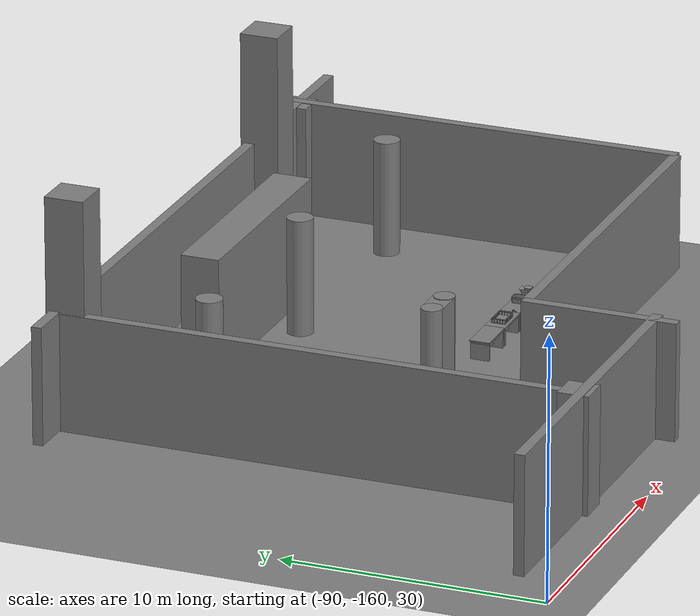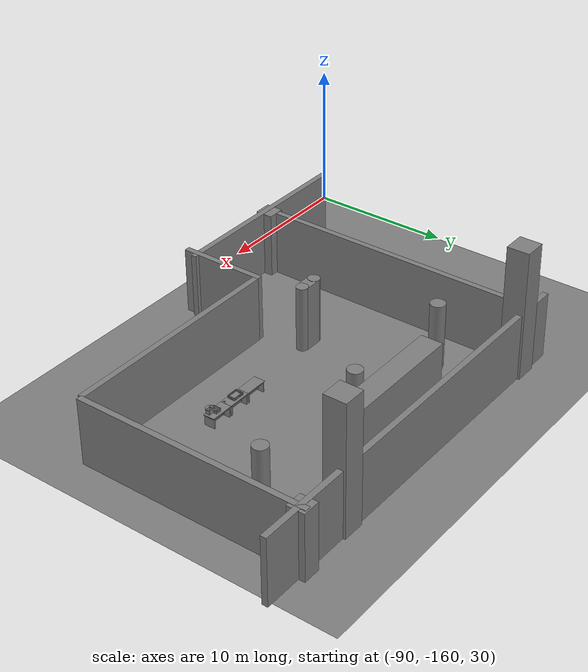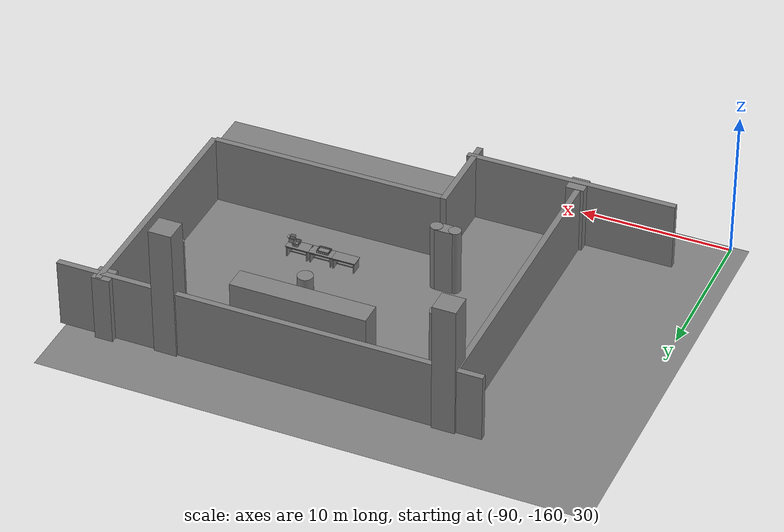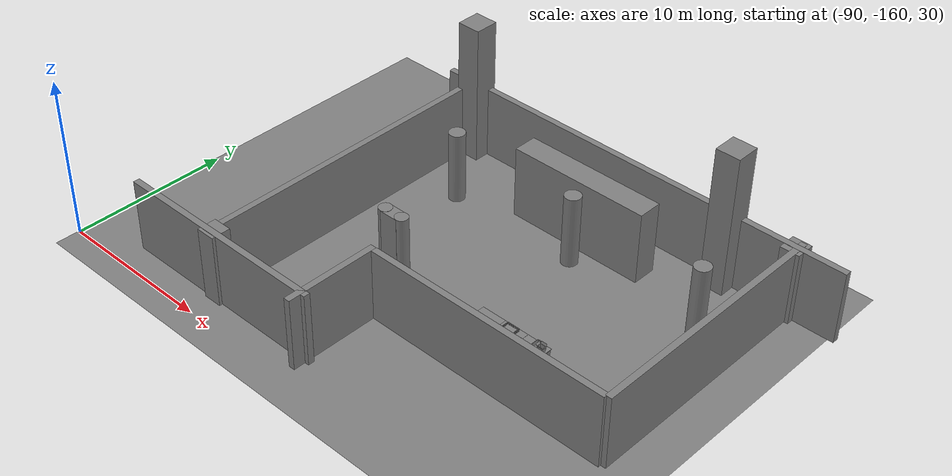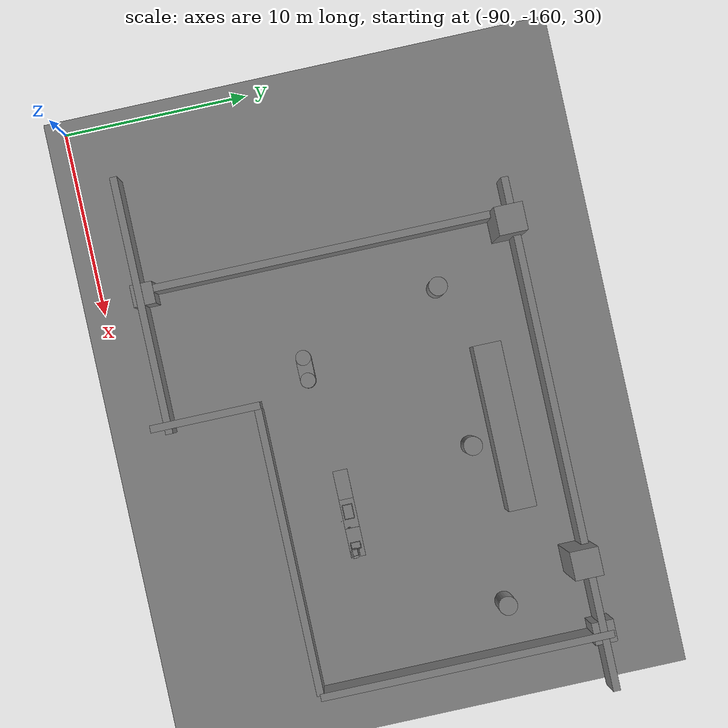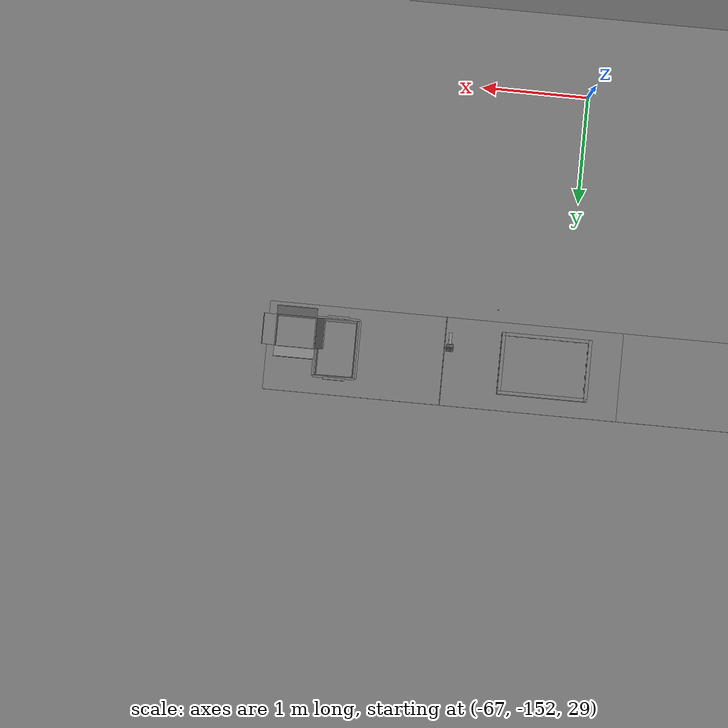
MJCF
<mujoco>
    <option gravity="0.000000000 0.000000000 -9.810000420" timestep="0.0049999999" integrator="implicitfast" density="1.225" viscosity="1.8000001e-05" noslip_iterations="10" iterations="100" sdf_iterations="50">
        <flag multiccd="disable"/>
    </option>
    <size memory="1000M"/>
    <compiler coordinate="local"/>
    <worldbody>
        <light cutoff="30" pos="0 1 1" dir="0 -1 -2"/>
        <light cutoff="30" pos="0 -1 1" dir="0 1 -2"/>
        <body pos="-64.866622925 -149.383972168 30.183746338" euler="89.999992371 89.999946594 0.000000000" name="openloong_gripper_2f85_fix_base_usda_bluebox_01">
            <geom contype="1" conaffinity="1" density="1000" type="box" material="" rgba="0.500000000 0.500000000 0.500000000 1.000000000" solimp="0.899999976 0.949999988 0.001000000" friction="1.000000000 0.005000000 0.000100000" solref="0.020000000 1.000000000" margin="0" condim="3" group="0" pos="0.276596069 0.187225342 0.000061035" quat="0.707107008 0.000077501 0.707106471 0.000077456" size="0.100000001 0.057999998 0.010000000" name="openloong_gripper_2f85_fix_base_usda_geom_4A08A09F_9054_41AC_892E_DBFC53AE1AC0"/>
            <geom contype="1" conaffinity="1" density="1000" type="box" material="" rgba="0.500000000 0.500000000 0.500000000 1.000000000" solimp="0.899999976 0.949999988 0.001000000" friction="1.000000000 0.005000000 0.000100000" solref="0.020000000 1.000000000" margin="0" condim="3" group="0" pos="0.000000000 0.002883911 0.000000000" quat="1.000000000 0.000000000 0.000000000 0.000000000" size="0.254000008 0.003000000 0.172000006" name="openloong_gripper_2f85_fix_base_usda_geom_5692C4FD_F0B7_4AA6_97C4_1E4947A94DB1"/>
            <geom contype="1" conaffinity="1" density="1000" type="box" material="" rgba="0.500000000 0.500000000 0.500000000 1.000000000" solimp="0.899999976 0.949999988 0.001000000" friction="1.000000000 0.005000000 0.000100000" solref="0.020000000 1.000000000" margin="0" condim="3" group="0" pos="0.000015259 0.124874115 0.173477173" quat="0.999796450 0.020176515 -0.000000015 0.000000030" size="0.259999990 0.119999997 0.007000000" name="openloong_gripper_2f85_fix_base_usda_geom_3F61E7CD_13C2_4184_A0B8_A4BB8586438D"/>
            <geom contype="1" conaffinity="1" density="1000" type="box" material="" rgba="0.500000000 0.500000000 0.500000000 1.000000000" solimp="0.899999976 0.949999988 0.001000000" friction="1.000000000 0.005000000 0.000100000" solref="0.020000000 1.000000000" margin="0" condim="3" group="0" pos="0.000015259 0.124874115 -0.173477173" quat="0.999796450 -0.020176545 -0.000000015 0.000000000" size="0.259999990 0.119999997 0.007000000" name="openloong_gripper_2f85_fix_base_usda_geom_253EB3CC_C2EA_4A91_B062_1B0B90089183"/>
            <geom contype="1" conaffinity="1" density="1000" type="box" material="" rgba="0.500000000 0.500000000 0.500000000 1.000000000" solimp="0.899999976 0.949999988 0.001000000" friction="1.000000000 0.005000000 0.000100000" solref="0.020000000 1.000000000" margin="0" condim="3" group="0" pos="0.000015259 0.214012146 0.188980103" quat="0.999913096 0.013176724 0.000000015 0.000000000" size="0.259999990 0.029999999 0.012500000" name="openloong_gripper_2f85_fix_base_usda_geom_C2242964_A439_47DE_B52A_087D51F2BCCE"/>
            <geom contype="1" conaffinity="1" density="1000" type="box" material="" rgba="0.500000000 0.500000000 0.500000000 1.000000000" solimp="0.899999976 0.949999988 0.001000000" friction="1.000000000 0.005000000 0.000100000" solref="0.020000000 1.000000000" margin="0" condim="3" group="0" pos="-0.258346558 0.125289917 0.001876831" quat="0.702796996 -0.020792052 0.710783184 0.020769238" size="0.189999998 0.119999997 0.009000000" name="openloong_gripper_2f85_fix_base_usda_geom_84FF8940_5E26_4340_86D1_DB350435A977"/>
            <geom contype="1" conaffinity="1" density="1000" type="box" material="" rgba="0.500000000 0.500000000 0.500000000 1.000000000" solimp="0.899999976 0.949999988 0.001000000" friction="1.000000000 0.005000000 0.000100000" solref="0.020000000 1.000000000" margin="0" condim="3" group="0" pos="0.000015259 0.214012146 -0.188980103" quat="0.999913096 -0.013176769 0.000000030 0.000000015" size="0.259999990 0.029999999 0.012500000" name="openloong_gripper_2f85_fix_base_usda_geom_F1BF6580_773D_4F7A_A2A5_51E1FE4AAEC9"/>
            <geom contype="1" conaffinity="1" density="1000" type="box" material="" rgba="0.500000000 0.500000000 0.500000000 1.000000000" solimp="0.899999976 0.949999988 0.001000000" friction="1.000000000 0.005000000 0.000100000" solref="0.020000000 1.000000000" margin="0" condim="3" group="0" pos="-0.276596069 0.187225342 0.000061035" quat="0.707106650 0.000077441 0.707106709 0.000077456" size="0.100000001 0.057999998 0.010000000" name="openloong_gripper_2f85_fix_base_usda_geom_4595124F_06AC_4F8F_A7C3_8776FA0FC334"/>
            <geom contype="1" conaffinity="1" density="1000" type="box" material="" rgba="0.500000000 0.500000000 0.500000000 1.000000000" solimp="0.899999976 0.949999988 0.001000000" friction="1.000000000 0.005000000 0.000100000" solref="0.020000000 1.000000000" margin="0" condim="3" group="0" pos="0.258346558 0.125289917 0.001876831" quat="0.702851534 0.018856451 0.710823834 -0.019329429" size="0.189999998 0.119999997 0.009000000" name="openloong_gripper_2f85_fix_base_usda_geom_82807A6B_EACE_48FF_82D1_5A78A7D1C4D4"/>
            <freejoint name="openloong_gripper_2f85_fix_base_usda_bluebox_01_joint"/>
            <site size="0.005000000 0.005000000 0.005000000" rgba="0.500000000 0.500000000 0.500000000 1.000000000" pos="0.000000000 0.000000000 0.000000000" quat="0.999961913 0.008726534 0.000000000 0.000000000" group="0" type="sphere" name="openloong_gripper_2f85_fix_base_usda_bluebox_01site"/>
        </body>
        <body pos="-64.496299744 -149.491867065 30.235729218" euler="0.000000000 0.000000000 89.999946594" name="openloong_gripper_2f85_fix_base_usda_cardboardbox_01">
            <geom contype="1" conaffinity="1" density="1000" type="box" material="" rgba="0.500000000 0.500000000 0.500000000 1.000000000" solimp="0.899999976 0.949999988 0.001000000" friction="1.000000000 0.005000000 0.000100000" solref="0.020000000 1.000000000" margin="0" condim="3" group="0" pos="-0.003166199 -0.004086494 0.005052090" quat="1.000000000 0.000000000 0.000000000 0.000000000" size="0.142499998 0.177500010 0.005000000" name="openloong_gripper_2f85_fix_base_usda_geom_1A6FFF37_936B_44F0_87ED_6CCE010C325D"/>
            <geom contype="1" conaffinity="1" density="1000" type="box" material="" rgba="0.500000000 0.500000000 0.500000000 1.000000000" solimp="0.899999976 0.949999988 0.001000000" friction="1.000000000 0.005000000 0.000100000" solref="0.020000000 1.000000000" margin="0" condim="3" group="0" pos="-0.003166199 0.170316696 0.150570869" quat="1.000000000 0.000000000 0.000000000 0.000000000" size="0.142499998 0.005000000 0.149999991" name="openloong_gripper_2f85_fix_base_usda_geom_46123709_1DE7_4F4C_819C_FD425435C14B"/>
            <geom contype="1" conaffinity="1" density="1000" type="box" material="" rgba="0.500000000 0.500000000 0.500000000 1.000000000" solimp="0.899999976 0.949999988 0.001000000" friction="1.000000000 0.005000000 0.000100000" solref="0.020000000 1.000000000" margin="0" condim="3" group="0" pos="-0.147399902 -0.005307198 0.150570869" quat="1.000000000 0.000000000 0.000000000 0.000000000" size="0.005000000 0.177500010 0.149999991" name="openloong_gripper_2f85_fix_base_usda_geom_DD8D2412_6171_4A11_9C68_CE666387C0E0"/>
            <geom contype="1" conaffinity="1" density="1000" type="box" material="" rgba="0.500000000 0.500000000 0.500000000 1.000000000" solimp="0.899999976 0.949999988 0.001000000" friction="1.000000000 0.005000000 0.000100000" solref="0.020000000 1.000000000" margin="0" condim="3" group="0" pos="0.140275955 -0.005307198 0.150570869" quat="1.000000000 0.000000000 0.000000000 0.000000000" size="0.005000000 0.177500010 0.149999991" name="openloong_gripper_2f85_fix_base_usda_geom_5F20A978_3E3A_45DF_874D_4412BE0D04E5"/>
            <geom contype="1" conaffinity="1" density="1000" type="box" material="" rgba="0.500000000 0.500000000 0.500000000 1.000000000" solimp="0.899999976 0.949999988 0.001000000" friction="1.000000000 0.005000000 0.000100000" solref="0.020000000 1.000000000" margin="0" condim="3" group="0" pos="-0.003166199 -0.181550980 0.150570869" quat="1.000000000 0.000000000 0.000000000 0.000000000" size="0.142499998 0.005000000 0.149999991" name="openloong_gripper_2f85_fix_base_usda_geom_F0A08252_68FD_452A_AFF0_8124FCB007A1"/>
            <freejoint name="openloong_gripper_2f85_fix_base_usda_cardboardbox_01_joint"/>
            <site size="0.005000000 0.005000000 0.005000000" rgba="0.500000000 0.500000000 0.500000000 1.000000000" pos="0.000000000 0.000000000 0.000000000" quat="0.999961913 0.008726535 0.000000000 0.000000000" group="0" type="sphere" name="openloong_gripper_2f85_fix_base_usda_site_0027EEC3_B4DF_4A28_9A63_30AC4BF977FD"/>
            <body pos="0.139160156 -0.004048347 0.301930904" euler="-179.999954224 49.383502960 179.999954224" name="openloong_gripper_2f85_fix_base_usda_A1_006">
                <geom contype="1" conaffinity="1" density="1000" type="box" material="" rgba="0.500000000 0.500000000 0.500000000 1.000000000" solimp="0.899999976 0.949999988 0.001000000" friction="1.000000000 0.005000000 0.000100000" solref="0.020000000 1.000000000" margin="0" condim="3" group="0" pos="-0.071587563 0.000009537 0.001745224" quat="0.999999881 0.000000000 0.000000000 0.000000000" size="0.071249999 0.179999992 0.002500000" name="openloong_gripper_2f85_fix_base_usda_geom_88266B7A_FA18_412F_BEB1_54FEEC389338"/>
                <joint armature="0" stiffness="0.07" damping="0.0099999998" axis="0.000000 1.000000 0.000000" type="hinge" name="openloong_gripper_2f85_fix_base_usda_A1_006"/>
            </body>
            <body pos="-0.145902634 -0.004086494 0.301938057" euler="-180.000000000 -60.000011444 -180.000000000" name="openloong_gripper_2f85_fix_base_usda_A2_006">
                <geom contype="1" conaffinity="1" density="1000" type="box" material="" rgba="0.500000000 0.500000000 0.500000000 1.000000000" solimp="0.899999976 0.949999988 0.001000000" friction="1.000000000 0.005000000 0.000100000" solref="0.020000000 1.000000000" margin="0" condim="3" group="0" pos="0.071268082 0.000009537 0.002717972" quat="0.000002921 0.000000000 -0.000000030 0.999999881" size="0.071249999 0.179999992 0.002500000" name="openloong_gripper_2f85_fix_base_usda_geom_81B2ACC7_1485_4DAE_A738_6C2A0C797642"/>
                <joint armature="0" stiffness="0.07" damping="0.0099999998" axis="0.000000 1.000000 0.000000" type="hinge" name="openloong_gripper_2f85_fix_base_usda_A2_006"/>
            </body>
            <body pos="-0.003385544 0.175991058 0.301930904" euler="-125.858116150 -0.000004561 0.000002331" name="openloong_gripper_2f85_fix_base_usda_B2_006">
                <geom contype="1" conaffinity="1" density="1000" type="box" material="" rgba="0.500000000 0.500000000 0.500000000 1.000000000" solimp="0.899999976 0.949999988 0.001000000" friction="1.000000000 0.005000000 0.000100000" solref="0.020000000 1.000000000" margin="0" condim="3" group="0" pos="0.000009537 -0.070939064 -0.002470016" quat="0.999614120 0.027776197 -0.000000015 0.000000030" size="0.137500003 0.064999998 0.005000000" name="openloong_gripper_2f85_fix_base_usda_geom_1342B25B_9895_45A6_B98F_2C8249F640E9"/>
                <joint armature="0" stiffness="0.07" damping="0.0099999998" axis="1.000000 0.000000 0.000000" type="hinge" name="openloong_gripper_2f85_fix_base_usda_B2_006"/>
            </body>
            <body pos="-0.003385544 -0.184140205 0.301938057" euler="147.805557251 0.000000000 0.000000000" name="openloong_gripper_2f85_fix_base_usda_B1_006">
                <geom contype="1" conaffinity="1" density="1000" type="box" material="" rgba="0.500000000 0.500000000 0.500000000 1.000000000" solimp="0.899999976 0.949999988 0.001000000" friction="1.000000000 0.005000000 0.000100000" solref="0.020000000 1.000000000" margin="0" condim="3" group="0" pos="-0.000028610 0.070202351 -0.002703667" quat="0.999614179 -0.027776167 0.000000000 0.000000000" size="0.137500003 0.064999998 0.005000000" name="openloong_gripper_2f85_fix_base_usda_geom_8D57EE97_5AA6_4F1E_BE69_B727BF3AD1EB"/>
                <joint armature="0" stiffness="0.07" damping="0.0099999998" axis="1.000000 0.000000 0.000000" type="hinge" name="openloong_gripper_2f85_fix_base_usda_B1_006"/>
            </body>
        </body>
        <body pos="-65.882858276 -149.481979370 30.229999542" euler="-64.487716675 0.000000000 0.000000000" name="openloong_gripper_2f85_fix_base_usda_Barcode">
            <geom contype="1" conaffinity="1" density="1000" type="box" material="" rgba="0.500000000 0.500000000 0.500000000 1.000000000" solimp="0.899999976 0.949999988 0.001000000" friction="1.000000000 0.005000000 0.000100000" solref="0.020000000 1.000000000" margin="0" condim="3" group="0" pos="0.000000000 0.013038635 0.001419067" quat="0.000000000 0.000000000 0.000000000 1.000000119" size="0.034000002 0.010000000 0.017999999" name="openloong_gripper_2f85_fix_base_usda_geom_7871B2D8_C72A_4E9C_82B6_5B8B889982C5"/>
            <geom contype="1" conaffinity="1" density="1000" type="box" material="" rgba="0.500000000 0.500000000 0.500000000 1.000000000" solimp="0.899999976 0.949999988 0.001000000" friction="1.000000000 0.005000000 0.000100000" solref="0.020000000 1.000000000" margin="0" condim="3" group="0" pos="0.000000000 -0.035301208 -0.007095337" quat="0.000000000 0.000000000 -0.043619365 0.999048233" size="0.028999999 0.010000000 0.020000000" name="openloong_gripper_2f85_fix_base_usda_geom_84359091_4BE4_4C2E_8002_2ABF461C1CAC"/>
            <geom contype="1" conaffinity="1" density="1000" type="box" material="" rgba="0.500000000 0.500000000 0.500000000 1.000000000" solimp="0.899999976 0.949999988 0.001000000" friction="1.000000000 0.005000000 0.000100000" solref="0.020000000 1.000000000" margin="0" condim="3" group="0" pos="0.000000000 -0.043411255 -0.011749268" quat="0.922262907 0.386563420 0.000000000 0.000000000" size="0.026000001 0.010000000 0.020000000" name="openloong_gripper_2f85_fix_base_usda_geom_E33A3ABE_0347_4BEC_AC31_4EE451808689"/>
            <geom contype="1" conaffinity="1" density="1000" type="box" material="" rgba="0.500000000 0.500000000 0.500000000 1.000000000" solimp="0.899999976 0.949999988 0.001000000" friction="1.000000000 0.005000000 0.000100000" solref="0.020000000 1.000000000" margin="0" condim="3" group="0" pos="0.000000000 -0.016967773 -0.031860352" quat="0.000000000 0.000000000 0.000000000 1.000000119" size="0.008000000 0.010000000 0.013000000" name="openloong_gripper_2f85_fix_base_usda_geom_DBB2183C_EA27_44B9_9C03_90F17982CF38"/>
            <geom contype="1" conaffinity="1" density="1000" type="box" material="" rgba="0.500000000 0.500000000 0.500000000 1.000000000" solimp="0.899999976 0.949999988 0.001000000" friction="1.000000000 0.005000000 0.000100000" solref="0.020000000 1.000000000" margin="0" condim="3" group="0" pos="0.000000000 -0.001869202 0.000312805" quat="0.953716993 0.300705761 0.000000000 0.000000000" size="0.032000002 0.010000000 0.018999999" name="openloong_gripper_2f85_fix_base_usda_geom_3417704E_AD1D_4E58_85D7_5507AECC2F27"/>
            <geom contype="1" conaffinity="1" density="1000" type="box" material="" rgba="0.500000000 0.500000000 0.500000000 1.000000000" solimp="0.899999976 0.949999988 0.001000000" friction="1.000000000 0.005000000 0.000100000" solref="0.020000000 1.000000000" margin="0" condim="3" group="0" pos="0.000000000 -0.019531250 -0.003173828" quat="0.953716993 0.300705761 0.000000000 0.000000000" size="0.030999999 0.010000000 0.020000000" name="openloong_gripper_2f85_fix_base_usda_geom_27763240_EF97_4150_B3C1_F6265C469228"/>
            <geom contype="1" conaffinity="1" density="1000" type="box" material="" rgba="0.500000000 0.500000000 0.500000000 1.000000000" solimp="0.899999976 0.949999988 0.001000000" friction="1.000000000 0.005000000 0.000100000" solref="0.020000000 1.000000000" margin="0" condim="3" group="0" pos="0.000000000 -0.035301208 -0.007095337" quat="0.953716993 0.300705761 0.000000000 0.000000000" size="0.028999999 0.010000000 0.020000000" name="openloong_gripper_2f85_fix_base_usda_geom_5E8485BC_C831_4174_9F7D_589393DCAAA2"/>
            <geom contype="1" conaffinity="1" density="1000" type="box" material="" rgba="0.500000000 0.500000000 0.500000000 1.000000000" solimp="0.899999976 0.949999988 0.001000000" friction="1.000000000 0.005000000 0.000100000" solref="0.020000000 1.000000000" margin="0" condim="3" group="0" pos="0.000000000 -0.042617798 -0.071121216" quat="0.000000000 0.000000000 0.000000000 1.000000119" size="0.013000000 0.021000000 0.059999999" name="openloong_gripper_2f85_fix_base_usda_geom_3E457227_D6A3_4715_8088_58C58547DDCA"/>
            <freejoint name="openloong_gripper_2f85_fix_base_usda_Barcode_joint"/>
            <site size="0.005000000 0.005000000 0.005000000" rgba="0.500000000 0.500000000 0.500000000 1.000000000" pos="0.000000000 0.000000000 0.000000000" quat="1.000000000 0.000000000 0.000000000 0.000000000" group="0" type="sphere" name="openloong_gripper_2f85_fix_base_usda_Barcode_site"/>
        </body>
        <body pos="-66.745018005 -149.392349243 30.184000015" euler="0.000000000 0.000000000 89.999946594" name="[22331394616085]_Basket_01">
            <geom contype="1" conaffinity="1" density="1000" type="box" material="" rgba="0.500000000 0.500000000 0.500000000 1.000000000" solimp="0.899999976 0.949999988 0.001000000" friction="1.000000000 0.005000000 0.000100000" solref="0.020000000 1.000000000" margin="0" condim="3" group="0" pos="-0.052425385 0.389207840 0.089787483" quat="0.707107008 0.000000000 0.000000000 0.707106411" size="0.014249999 0.014249999 0.059999999" name="[22331394616085]_geom_0A1D5F4A_C595_4512_9A91_9B38D0B2813A"/>
            <geom contype="1" conaffinity="1" density="1000" type="box" material="" rgba="0.500000000 0.500000000 0.500000000 1.000000000" solimp="0.899999976 0.949999988 0.001000000" friction="1.000000000 0.005000000 0.000100000" solref="0.020000000 1.000000000" margin="0" condim="3" group="0" pos="0.264015198 -0.133043289 0.089787483" quat="0.707107008 0.000000000 0.000000000 0.707106411" size="0.014249999 0.014249999 0.059999999" name="[22331394616085]_geom_E2B60042_0CB8_4152_BDC7_2D6C15D27445"/>
            <geom contype="1" conaffinity="1" density="1000" type="box" material="" rgba="0.500000000 0.500000000 0.500000000 1.000000000" solimp="0.899999976 0.949999988 0.001000000" friction="1.000000000 0.005000000 0.000100000" solref="0.020000000 1.000000000" margin="0" condim="3" group="0" pos="-0.264015198 -0.265548706 0.089793205" quat="0.707107008 0.000000000 0.000000000 0.707106411" size="0.014249999 0.014249999 0.059999999" name="[22331394616085]_geom_BA2F4FC6_6C7B_40F8_A531_3F928FC3149A"/>
            <geom contype="1" conaffinity="1" density="1000" type="box" material="" rgba="0.500000000 0.500000000 0.500000000 1.000000000" solimp="0.899999976 0.949999988 0.001000000" friction="1.000000000 0.005000000 0.000100000" solref="0.020000000 1.000000000" margin="0" condim="3" group="0" pos="-0.160263062 -0.389322281 0.089793205" quat="0.707107008 0.000000000 0.000000000 0.707106411" size="0.014249999 0.014249999 0.059999999" name="[22331394616085]_geom_E63FDFD9_FBEF_43DC_ADA9_C3556DBE23B7"/>
            <geom contype="1" conaffinity="1" density="1000" type="box" material="" rgba="0.500000000 0.500000000 0.500000000 1.000000000" solimp="0.899999976 0.949999988 0.001000000" friction="1.000000000 0.005000000 0.000100000" solref="0.020000000 1.000000000" margin="0" condim="3" group="0" pos="0.162265778 -0.389322281 0.089787483" quat="0.707107008 0.000000000 0.000000000 0.707106411" size="0.014249999 0.014249999 0.059999999" name="[22331394616085]_geom_62D6D91C_CC2C_42B4_812B_205FBA5DCAA4"/>
            <geom contype="1" conaffinity="1" density="1000" type="box" material="" rgba="0.500000000 0.500000000 0.500000000 1.000000000" solimp="0.899999976 0.949999988 0.001000000" friction="1.000000000 0.005000000 0.000100000" solref="0.020000000 1.000000000" margin="0" condim="3" group="0" pos="0.264015198 0.389207840 0.089787483" quat="0.707107008 0.000000000 0.000000000 0.707106411" size="0.014249999 0.014249999 0.059999999" name="[22331394616085]_geom_F9B9B658_09CE_4E81_843A_10AAC2792702"/>
            <geom contype="1" conaffinity="1" density="1000" type="box" material="" rgba="0.500000000 0.500000000 0.500000000 1.000000000" solimp="0.899999976 0.949999988 0.001000000" friction="1.000000000 0.005000000 0.000100000" solref="0.020000000 1.000000000" margin="0" condim="3" group="0" pos="-0.264015198 -0.133043289 0.089793205" quat="0.707107008 0.000000000 0.000000000 0.707106411" size="0.014249999 0.014249999 0.059999999" name="[22331394616085]_geom_A5391053_5979_456C_89B2_DBDE0E34BBC4"/>
            <geom contype="1" conaffinity="1" density="1000" type="box" material="" rgba="0.500000000 0.500000000 0.500000000 1.000000000" solimp="0.899999976 0.949999988 0.001000000" friction="1.000000000 0.005000000 0.000100000" solref="0.020000000 1.000000000" margin="0" condim="3" group="0" pos="-0.264026642 0.269256592 0.089793205" quat="0.707107008 0.000000000 0.000000000 0.707106411" size="0.014249999 0.014249999 0.059999999" name="[22331394616085]_geom_F7050E05_56D3_4013_B3C6_917EF898EED3"/>
            <geom contype="1" conaffinity="1" density="1000" type="box" material="" rgba="0.500000000 0.500000000 0.500000000 1.000000000" solimp="0.899999976 0.949999988 0.001000000" friction="1.000000000 0.005000000 0.000100000" solref="0.020000000 1.000000000" margin="0" condim="3" group="0" pos="0.054462433 0.389207840 0.089787483" quat="0.707107008 0.000000000 0.000000000 0.707106411" size="0.014249999 0.014249999 0.059999999" name="[22331394616085]_geom_62A8076F_5143_47F9_BC72_9C5D27F6776D"/>
            <geom contype="1" conaffinity="1" density="1000" type="box" material="" rgba="0.500000000 0.500000000 0.500000000 1.000000000" solimp="0.899999976 0.949999988 0.001000000" friction="1.000000000 0.005000000 0.000100000" solref="0.020000000 1.000000000" margin="0" condim="3" group="0" pos="0.054462433 -0.389322281 0.089787483" quat="0.707107008 0.000000000 0.000000000 0.707106411" size="0.014249999 0.014249999 0.059999999" name="[22331394616085]_geom_E4D1C9BF_A1D6_46AC_AA01_D86DB0E34194"/>
            <geom contype="1" conaffinity="1" density="1000" type="box" material="" rgba="0.500000000 0.500000000 0.500000000 1.000000000" solimp="0.899999976 0.949999988 0.001000000" friction="1.000000000 0.005000000 0.000100000" solref="0.020000000 1.000000000" margin="0" condim="3" group="0" pos="0.264015198 0.269256592 0.089793205" quat="0.707107008 0.000000000 0.000000000 0.707106411" size="0.014249999 0.014249999 0.059999999" name="[22331394616085]_geom_D66F79F0_91C9_4C34_A298_4302E33FDDB3"/>
            <geom contype="1" conaffinity="1" density="1000" type="box" material="" rgba="0.500000000 0.500000000 0.500000000 1.000000000" solimp="0.899999976 0.949999988 0.001000000" friction="1.000000000 0.005000000 0.000100000" solref="0.020000000 1.000000000" margin="0" condim="3" group="0" pos="0.264015198 -0.389322281 0.089787483" quat="0.707107008 0.000000000 0.000000000 0.707106411" size="0.014249999 0.014249999 0.059999999" name="[22331394616085]_geom_3341A09C_7085_4F3A_8142_BB4FC5045ACE"/>
            <geom contype="1" conaffinity="1" density="1000" type="box" material="" rgba="0.500000000 0.500000000 0.500000000 1.000000000" solimp="0.899999976 0.949999988 0.001000000" friction="1.000000000 0.005000000 0.000100000" solref="0.020000000 1.000000000" margin="0" condim="3" group="0" pos="0.000000000 0.000000000 0.015998840" quat="0.707107008 0.000000000 0.000000000 0.707106411" size="0.403499991 0.279000014 0.015750000" name="[22331394616085]_geom_413774A6_EBD0_47DF_90B9_B6F2DA40642E"/>
            <geom contype="1" conaffinity="1" density="1000" type="box" material="" rgba="0.500000000 0.500000000 0.500000000 1.000000000" solimp="0.899999976 0.949999988 0.001000000" friction="1.000000000 0.005000000 0.000100000" solref="0.020000000 1.000000000" margin="0" condim="3" group="0" pos="0.000000000 -0.389476776 0.163619041" quat="0.707107008 0.000000000 0.000000000 0.707106411" size="0.015000000 0.277500004 0.015750000" name="[22331394616085]_geom_074E9D42_62BE_4E17_9882_E7539FDDECF0"/>
            <geom contype="1" conaffinity="1" density="1000" type="box" material="" rgba="0.500000000 0.500000000 0.500000000 1.000000000" solimp="0.899999976 0.949999988 0.001000000" friction="1.000000000 0.005000000 0.000100000" solref="0.020000000 1.000000000" margin="0" condim="3" group="0" pos="0.162265778 0.389207840 0.089787483" quat="0.707107008 0.000000000 0.000000000 0.707106411" size="0.014249999 0.014249999 0.059999999" name="[22331394616085]_geom_139DF774_3853_44CB_88AA_43EB81DC7C9F"/>
            <geom contype="1" conaffinity="1" density="1000" type="box" material="" rgba="0.500000000 0.500000000 0.500000000 1.000000000" solimp="0.899999976 0.949999988 0.001000000" friction="1.000000000 0.005000000 0.000100000" solref="0.020000000 1.000000000" margin="0" condim="3" group="0" pos="0.000000000 0.389471054 0.163619041" quat="0.707107008 0.000000000 0.000000000 0.707106411" size="0.015000000 0.277500004 0.015750000" name="[22331394616085]_geom_AD72855E_17ED_4E71_89D3_66226EB39524"/>
            <geom contype="1" conaffinity="1" density="1000" type="box" material="" rgba="0.500000000 0.500000000 0.500000000 1.000000000" solimp="0.899999976 0.949999988 0.001000000" friction="1.000000000 0.005000000 0.000100000" solref="0.020000000 1.000000000" margin="0" condim="3" group="0" pos="-0.263511658 0.000000000 0.163619041" quat="0.707107008 0.000000000 0.000000000 0.707106411" size="0.403499991 0.015000000 0.015750000" name="[22331394616085]_geom_0881B379_ED25_4969_8067_5B2C3611D842"/>
            <geom contype="1" conaffinity="1" density="1000" type="box" material="" rgba="0.500000000 0.500000000 0.500000000 1.000000000" solimp="0.899999976 0.949999988 0.001000000" friction="1.000000000 0.005000000 0.000100000" solref="0.020000000 1.000000000" margin="0" condim="3" group="0" pos="-0.264015198 0.141334534 0.089793205" quat="0.707107008 0.000000000 0.000000000 0.707106411" size="0.014249999 0.014249999 0.059999999" name="[22331394616085]_geom_E6CE2FD5_0A86_4B5A_A668_5104B044EEFD"/>
            <geom contype="1" conaffinity="1" density="1000" type="box" material="" rgba="0.500000000 0.500000000 0.500000000 1.000000000" solimp="0.899999976 0.949999988 0.001000000" friction="1.000000000 0.005000000 0.000100000" solref="0.020000000 1.000000000" margin="0" condim="3" group="0" pos="0.264015198 -0.265548706 0.089787483" quat="0.707107008 0.000000000 0.000000000 0.707106411" size="0.014249999 0.014249999 0.059999999" name="[22331394616085]_geom_48A522E1_9E7E_4870_9A75_B3B88F4EB5DB"/>
            <geom contype="1" conaffinity="1" density="1000" type="box" material="" rgba="0.500000000 0.500000000 0.500000000 1.000000000" solimp="0.899999976 0.949999988 0.001000000" friction="1.000000000 0.005000000 0.000100000" solref="0.020000000 1.000000000" margin="0" condim="3" group="0" pos="-0.160263062 0.389207840 0.089787483" quat="0.707107008 0.000000000 0.000000000 0.707106411" size="0.014249999 0.014249999 0.059999999" name="[22331394616085]_geom_F51AE001_C873_448C_8B68_F0F8881ED565"/>
            <geom contype="1" conaffinity="1" density="1000" type="box" material="" rgba="0.500000000 0.500000000 0.500000000 1.000000000" solimp="0.899999976 0.949999988 0.001000000" friction="1.000000000 0.005000000 0.000100000" solref="0.020000000 1.000000000" margin="0" condim="3" group="0" pos="-0.052425385 -0.389322281 0.089787483" quat="0.707107008 0.000000000 0.000000000 0.707106411" size="0.014249999 0.014249999 0.059999999" name="[22331394616085]_geom_866FBDCF_3BC9_4147_8B9B_6C3191BAB4FA"/>
            <geom contype="1" conaffinity="1" density="1000" type="box" material="" rgba="0.500000000 0.500000000 0.500000000 1.000000000" solimp="0.899999976 0.949999988 0.001000000" friction="1.000000000 0.005000000 0.000100000" solref="0.020000000 1.000000000" margin="0" condim="3" group="0" pos="-0.264026642 -0.389322281 0.089793205" quat="0.707107008 0.000000000 0.000000000 0.707106411" size="0.014249999 0.014249999 0.059999999" name="[22331394616085]_geom_EC87E3EC_06F4_46CB_8926_666C193A277C"/>
            <geom contype="1" conaffinity="1" density="1000" type="box" material="" rgba="0.500000000 0.500000000 0.500000000 1.000000000" solimp="0.899999976 0.949999988 0.001000000" friction="1.000000000 0.005000000 0.000100000" solref="0.020000000 1.000000000" margin="0" condim="3" group="0" pos="0.264015198 0.141334534 0.089787483" quat="0.707107008 0.000000000 0.000000000 0.707106411" size="0.014249999 0.014249999 0.059999999" name="[22331394616085]_geom_BD700D1C_7171_4FD0_A248_0F01D0AC5E76"/>
            <geom contype="1" conaffinity="1" density="1000" type="box" material="" rgba="0.500000000 0.500000000 0.500000000 1.000000000" solimp="0.899999976 0.949999988 0.001000000" friction="1.000000000 0.005000000 0.000100000" solref="0.020000000 1.000000000" margin="0" condim="3" group="0" pos="-0.264015198 0.389207840 0.089793205" quat="0.707107008 0.000000000 0.000000000 0.707106411" size="0.014249999 0.014249999 0.059999999" name="[22331394616085]_geom_6A2F79C5_AC81_45E8_946E_C46D18A06427"/>
            <geom contype="1" conaffinity="1" density="1000" type="box" material="" rgba="0.500000000 0.500000000 0.500000000 1.000000000" solimp="0.899999976 0.949999988 0.001000000" friction="1.000000000 0.005000000 0.000100000" solref="0.020000000 1.000000000" margin="0" condim="3" group="0" pos="0.264015198 0.004480362 0.089787483" quat="0.707107008 0.000000000 0.000000000 0.707106411" size="0.014249999 0.014249999 0.059999999" name="[22331394616085]_geom_C625AF05_5C0C_460A_AFE5_C88775BFCBF0"/>
            <geom contype="1" conaffinity="1" density="1000" type="box" material="" rgba="0.500000000 0.500000000 0.500000000 1.000000000" solimp="0.899999976 0.949999988 0.001000000" friction="1.000000000 0.005000000 0.000100000" solref="0.020000000 1.000000000" margin="0" condim="3" group="0" pos="0.263694763 -0.000011444 0.163619041" quat="0.707107008 0.000000000 0.000000000 0.707106411" size="0.403499991 0.015000000 0.015750000" name="[22331394616085]_geom_040733EC_7F5E_469E_A44F_2CD90BC3A54A"/>
            <geom contype="1" conaffinity="1" density="1000" type="box" material="" rgba="0.500000000 0.500000000 0.500000000 1.000000000" solimp="0.899999976 0.949999988 0.001000000" friction="1.000000000 0.005000000 0.000100000" solref="0.020000000 1.000000000" margin="0" condim="3" group="0" pos="-0.264015198 0.004480362 0.089793205" quat="0.707107008 0.000000000 0.000000000 0.707106411" size="0.014249999 0.014249999 0.059999999" name="[22331394616085]_geom_E4391442_9A83_449F_8559_2CB4A9A36D24"/>
            <freejoint name="[22331394616085]_joint_16B1E200_413B_42A6_8AEB_BE492CB24846"/>
        </body>
        <body pos="0.000000000 0.000000000 0.000000000" euler="0.000000000 0.000000000 0.000000000" name="Static Objects_Static Objects">
            <geom contype="1" conaffinity="1" density="1000" type="box" material="" rgba="0.500000000 0.500000000 0.500000000 1.000000000" solimp="0.899999976 0.949999988 0.001000000" friction="1.000000000 0.005000000 0.000100000" solref="0.020000000 1.000000000" margin="0" condim="3" group="0" pos="-67.544113159 -149.365814209 29.727830887" quat="0.500000417 0.499999970 0.499999553 0.499999970" size="0.381000012 0.319999993 0.041000001" name="Static Objects_geom_D6DB1826_3FC4_4FB4_80B4_2E429C941BFB"/>
            <geom contype="1" conaffinity="1" density="1000" type="box" material="" rgba="0.500000000 0.500000000 0.500000000 1.000000000" solimp="0.899999976 0.949999988 0.001000000" friction="1.000000000 0.005000000 0.000100000" solref="0.020000000 1.000000000" margin="0" condim="3" group="0" pos="-68.239501953 -149.365814209 30.086868286" quat="0.500000417 0.499999970 0.499999553 0.499999970" size="0.370999992 0.039500002 0.745000005" name="Static Objects_geom_476F02D5_25C9_4C89_920A_618DF7199C94"/>
            <geom contype="1" conaffinity="1" density="1000" type="box" material="" rgba="0.500000000 0.500000000 0.500000000 1.000000000" solimp="0.899999976 0.949999988 0.001000000" friction="1.000000000 0.005000000 0.000100000" solref="0.020000000 1.000000000" margin="0" condim="3" group="0" pos="-68.239501953 -149.365814209 30.147235870" quat="0.500000417 0.499999970 0.499999553 0.499999970" size="0.400000006 0.022000000 0.800000012" name="Static Objects_geom_884D96DF_EEB1_4C54_9FB1_77DD4E5908ED"/>
            <geom contype="1" conaffinity="1" density="1000" type="box" material="" rgba="0.500000000 0.500000000 0.500000000 1.000000000" solimp="0.899999976 0.949999988 0.001000000" friction="1.000000000 0.005000000 0.000100000" solref="0.020000000 1.000000000" margin="0" condim="3" group="0" pos="-68.934890747 -149.365814209 29.727830887" quat="0.500000417 0.499999970 0.499999553 0.499999970" size="0.381000012 0.319999993 0.041000001" name="Static Objects_geom_138C6287_FC84_46F2_B617_67A0784491BE"/>
            <geom contype="1" conaffinity="1" density="1000" type="box" material="" rgba="0.500000000 0.500000000 0.500000000 1.000000000" solimp="0.899999976 0.949999988 0.001000000" friction="1.000000000 0.005000000 0.000100000" solref="0.020000000 1.000000000" margin="0" condim="3" group="0" pos="-68.239501953 -149.365814209 29.561563492" quat="0.500000417 0.499999970 0.499999553 0.499999970" size="0.020000000 0.022000000 0.660000026" name="Static Objects_geom_450A23FE_D934_47E3_8677_0B6D983E2442"/>
            <geom contype="1" conaffinity="1" density="1000" type="box" material="" rgba="0.500000000 0.500000000 0.500000000 1.000000000" solimp="0.899999976 0.949999988 0.001000000" friction="1.000000000 0.005000000 0.000100000" solref="0.020000000 1.000000000" margin="0" condim="3" group="0" pos="-65.945671082 -149.365814209 29.727830887" quat="0.500000417 0.499999970 0.499999553 0.499999970" size="0.381000012 0.319999993 0.041000001" name="Static Objects_geom_D7264951_4D54_4128_AB4E_C4ACB734F336"/>
            <geom contype="1" conaffinity="1" density="1000" type="box" material="" rgba="0.500000000 0.500000000 0.500000000 1.000000000" solimp="0.899999976 0.949999988 0.001000000" friction="1.000000000 0.005000000 0.000100000" solref="0.020000000 1.000000000" margin="0" condim="3" group="0" pos="-66.641059875 -149.365814209 30.086868286" quat="0.500000417 0.499999970 0.499999553 0.499999970" size="0.370999992 0.039500002 0.745000005" name="Static Objects_geom_38C34D44_3A2E_43CF_99C8_2484A296BECC"/>
            <geom contype="1" conaffinity="1" density="1000" type="box" material="" rgba="0.500000000 0.500000000 0.500000000 1.000000000" solimp="0.899999976 0.949999988 0.001000000" friction="1.000000000 0.005000000 0.000100000" solref="0.020000000 1.000000000" margin="0" condim="3" group="0" pos="-66.641059875 -149.365814209 30.147235870" quat="0.500000417 0.499999970 0.499999553 0.499999970" size="0.400000006 0.022000000 0.800000012" name="Static Objects_geom_04330C15_B7DA_4765_86B7_D7CCD099CDE9"/>
            <geom contype="1" conaffinity="1" density="1000" type="box" material="" rgba="0.500000000 0.500000000 0.500000000 1.000000000" solimp="0.899999976 0.949999988 0.001000000" friction="1.000000000 0.005000000 0.000100000" solref="0.020000000 1.000000000" margin="0" condim="3" group="0" pos="-67.336448669 -149.365814209 29.727830887" quat="0.500000417 0.499999970 0.499999553 0.499999970" size="0.381000012 0.319999993 0.041000001" name="Static Objects_geom_4D9DD685_2824_419E_9AEB_3CA16710FFD3"/>
            <geom contype="1" conaffinity="1" density="1000" type="box" material="" rgba="0.500000000 0.500000000 0.500000000 1.000000000" solimp="0.899999976 0.949999988 0.001000000" friction="1.000000000 0.005000000 0.000100000" solref="0.020000000 1.000000000" margin="0" condim="3" group="0" pos="-66.641059875 -149.365814209 29.561563492" quat="0.500000417 0.499999970 0.499999553 0.499999970" size="0.020000000 0.022000000 0.660000026" name="Static Objects_geom_8E7F0D51_DAF3_4C34_AB16_03B116F118CD"/>
            <geom contype="1" conaffinity="1" density="1000" type="box" material="" rgba="0.500000000 0.500000000 0.500000000 1.000000000" solimp="0.899999976 0.949999988 0.001000000" friction="1.000000000 0.005000000 0.000100000" solref="0.020000000 1.000000000" margin="0" condim="3" group="0" pos="-64.338577271 -149.365814209 29.727830887" quat="0.500000417 0.499999970 0.499999553 0.499999970" size="0.381000012 0.319999993 0.041000001" name="Static Objects_geom_552EA5D7_4C00_497D_85F1_F0B8D2455E1D"/>
            <geom contype="1" conaffinity="1" density="1000" type="box" material="" rgba="0.500000000 0.500000000 0.500000000 1.000000000" solimp="0.899999976 0.949999988 0.001000000" friction="1.000000000 0.005000000 0.000100000" solref="0.020000000 1.000000000" margin="0" condim="3" group="0" pos="-65.033966064 -149.365814209 30.086868286" quat="0.500000417 0.499999970 0.499999553 0.499999970" size="0.370999992 0.039500002 0.745000005" name="Static Objects_geom_1E450D9B_26EE_475F_A44F_6E622F7436BB"/>
            <geom contype="1" conaffinity="1" density="1000" type="box" material="" rgba="0.500000000 0.500000000 0.500000000 1.000000000" solimp="0.899999976 0.949999988 0.001000000" friction="1.000000000 0.005000000 0.000100000" solref="0.020000000 1.000000000" margin="0" condim="3" group="0" pos="-65.033966064 -149.365814209 30.147235870" quat="0.500000417 0.499999970 0.499999553 0.499999970" size="0.400000006 0.022000000 0.800000012" name="Static Objects_geom_44629CEE_86B4_40EE_8E18_1D38F7540610"/>
            <geom contype="1" conaffinity="1" density="1000" type="box" material="" rgba="0.500000000 0.500000000 0.500000000 1.000000000" solimp="0.899999976 0.949999988 0.001000000" friction="1.000000000 0.005000000 0.000100000" solref="0.020000000 1.000000000" margin="0" condim="3" group="0" pos="-65.729354858 -149.365814209 29.727830887" quat="0.500000417 0.499999970 0.499999553 0.499999970" size="0.381000012 0.319999993 0.041000001" name="Static Objects_geom_69FB3C21_3081_4E39_9CD2_9193D18A5D63"/>
            <geom contype="1" conaffinity="1" density="1000" type="box" material="" rgba="0.500000000 0.500000000 0.500000000 1.000000000" solimp="0.899999976 0.949999988 0.001000000" friction="1.000000000 0.005000000 0.000100000" solref="0.020000000 1.000000000" margin="0" condim="3" group="0" pos="-65.033966064 -149.365814209 29.561563492" quat="0.500000417 0.499999970 0.499999553 0.499999970" size="0.020000000 0.022000000 0.660000026" name="Static Objects_geom_B06F4CF8_DE18_480F_B891_BF2501064105"/>
            <geom contype="1" conaffinity="1" density="1000" type="box" material="" rgba="0.500000000 0.500000000 0.500000000 1.000000000" solimp="0.899999976 0.949999988 0.001000000" friction="1.000000000 0.005000000 0.000100000" solref="0.020000000 1.000000000" margin="0" condim="3" group="0" pos="-61.754566193 -137.853729248 33.906845093" quat="0.707107067 0.000000000 0.000000000 0.707106471" size="0.759999990 0.759999990 4.500000000" name="Static Objects_geom_C24B5B9D_E65D_4925_B060_2B93E2912E95"/>
            <geom contype="1" conaffinity="1" density="1000" type="box" material="" rgba="0.500000000 0.500000000 0.500000000 1.000000000" solimp="0.899999976 0.949999988 0.001000000" friction="1.000000000 0.005000000 0.000100000" solref="0.020000000 1.000000000" margin="0" condim="3" group="0" pos="-57.511135101 -144.927108765 31.707921982" quat="1.000000000 0.000000000 0.000000000 0.000000000" size="0.200000003 8.000000000 2.299999952" name="Static Objects_geom_3936E3E7_B549_4588_8613_00C2F5090980"/>
            <geom contype="1" conaffinity="1" density="1000" type="box" material="" rgba="0.500000000 0.500000000 0.500000000 1.000000000" solimp="0.899999976 0.949999988 0.001000000" friction="1.000000000 0.005000000 0.000100000" solref="0.020000000 1.000000000" margin="0" condim="3" group="0" pos="-80.517646790 -157.574050903 31.688196182" quat="0.707107067 0.000000000 0.000000000 0.707106471" size="0.600000024 0.600000024 2.299999952" name="Static Objects_geom_4710F66D_C8DA_4187_BE73_1D36174121E8"/>
            <geom contype="1" conaffinity="1" density="1000" type="box" material="" rgba="0.500000000 0.500000000 0.500000000 1.000000000" solimp="0.899999976 0.949999988 0.001000000" friction="1.000000000 0.005000000 0.000100000" solref="0.020000000 1.000000000" margin="0" condim="3" group="0" pos="-80.711044312 -147.414932251 31.666158676" quat="1.000000000 0.000000000 0.000000000 0.000000000" size="0.200000003 10.000000000 2.299999952" name="Static Objects_geom_F0AA8449_41A7_4D6D_9D9F_E200A4C75076"/>
            <geom contype="1" conaffinity="1" density="1000" type="box" material="" rgba="0.500000000 0.500000000 0.500000000 1.000000000" solimp="0.899999976 0.949999988 0.001000000" friction="1.000000000 0.005000000 0.000100000" solref="0.020000000 1.000000000" margin="0" condim="3" group="0" pos="-57.687217712 -137.434692383 31.688196182" quat="0.707107067 0.000000000 0.000000000 0.707106471" size="0.600000024 0.600000024 2.299999952" name="Static Objects_geom_3EF51F12_266C_440C_AC3E_8CDB8AD9B9EF"/>
            <geom contype="1" conaffinity="1" density="1000" type="box" material="" rgba="0.500000000 0.500000000 0.500000000 1.000000000" solimp="0.899999976 0.949999988 0.001000000" friction="1.000000000 0.005000000 0.000100000" solref="0.020000000 1.000000000" margin="0" condim="3" group="0" pos="-69.537033081 -140.263229370 31.714921951" quat="0.707107067 0.000000000 0.000000000 0.707106471" size="0.759999990 4.500000000 2.299999952" name="Static Objects_geom_560E90BA_57A6_4409_8AD2_C7A59F708B4E"/>
            <geom contype="1" conaffinity="1" density="1000" type="box" material="" rgba="0.500000000 0.500000000 0.500000000 1.000000000" solimp="0.899999976 0.949999988 0.001000000" friction="1.000000000 0.005000000 0.000100000" solref="0.020000000 1.000000000" margin="0" condim="3" group="0" pos="-80.073638916 -137.853713989 33.906845093" quat="0.707107067 0.000000000 0.000000000 0.707106471" size="0.759999990 0.759999990 4.500000000" name="Static Objects_geom_C285F7B2_1F91_438F_B361_1B63369FE76B"/>
            <geom contype="1" conaffinity="1" density="1000" type="box" material="" rgba="0.500000000 0.500000000 0.500000000 1.000000000" solimp="0.899999976 0.949999988 0.001000000" friction="1.000000000 0.005000000 0.000100000" solref="0.020000000 1.000000000" margin="0" condim="3" group="0" pos="-73.406707764 -155.734664917 31.707921982" quat="1.000000000 0.000000000 0.000000000 0.000000000" size="0.200000003 3.000000000 2.299999952" name="Static Objects_geom_33542823_5057_4D2D_8918_D09C371FBD8D"/>
            <geom contype="1" conaffinity="1" density="1000" type="box" material="" rgba="0.500000000 0.500000000 0.500000000 1.000000000" solimp="0.899999976 0.949999988 0.001000000" friction="1.000000000 0.005000000 0.000100000" solref="0.020000000 1.000000000" margin="0" condim="3" group="0" pos="-68.497543335 -137.448257446 31.707921982" quat="0.707107067 0.000000000 0.000000000 0.707106471" size="0.200000003 14.000000000 2.299999952" name="Static Objects_geom_E62FA4F2_0AEF_48CD_8CC1_EC4CA68D6089"/>
            <geom contype="1" conaffinity="1" density="1000" type="cylinder" material="" rgba="0.500000000 0.500000000 0.500000000 1.000000000" solimp="0.899999976 0.949999988 0.001000000" friction="1.000000000 0.005000000 0.000100000" solref="0.020000000 1.000000000" margin="0" condim="3" group="0" pos="-68.868522644 -142.134506226 31.711090088" quat="0.707107067 0.000000000 0.000000000 0.707106471" size="0.509999990 2.299999952 1.000000000" name="Static Objects_geom_7D714432_D882_40C2_BBEF_0C07BD22B5F0"/>
            <geom contype="1" conaffinity="1" density="1000" type="plane" material="" rgba="0.500000000 0.500000000 0.500000000 1.000000000" solimp="0.899999976 0.949999988 0.001000000" friction="1.000000000 0.005000000 0.000100000" solref="0.020000000 1.000000000" margin="0" condim="3" group="0" pos="-72.873703003 -147.131927490 29.409669876" quat="1.000000000 0.000000000 0.000000000 0.000000000" size="18.000000000 14.000000000 1.000000000" name="Static Objects_geom_51F5F8E9_F642_4B0F_85A7_EF793BE59FF7"/>
            <geom contype="1" conaffinity="1" density="1000" type="box" material="" rgba="0.500000000 0.500000000 0.500000000 1.000000000" solimp="0.899999976 0.949999988 0.001000000" friction="1.000000000 0.005000000 0.000100000" solref="0.020000000 1.000000000" margin="0" condim="3" group="0" pos="-79.943580627 -157.782272339 31.707921982" quat="0.707107067 0.000000000 0.000000000 0.707106471" size="0.200000003 7.000000000 2.299999952" name="Static Objects_geom_6BBADFC1_8ABF_4EEF_9018_F4C408B85686"/>
            <geom contype="1" conaffinity="1" density="1000" type="box" material="" rgba="0.500000000 0.500000000 0.500000000 1.000000000" solimp="0.899999976 0.949999988 0.001000000" friction="1.000000000 0.005000000 0.000100000" solref="0.020000000 1.000000000" margin="0" condim="3" group="0" pos="-65.421028137 -152.903442383 31.707921982" quat="0.707107067 0.000000000 0.000000000 0.707106471" size="0.200000003 7.800000191 2.299999952" name="Static Objects_geom_7E98EC98_1C35_4DBC_A184_7DF1B7BD905D"/>
            <geom contype="1" conaffinity="1" density="1000" type="box" material="" rgba="0.500000000 0.500000000 0.500000000 1.000000000" solimp="0.899999976 0.949999988 0.001000000" friction="1.000000000 0.005000000 0.000100000" solref="0.020000000 1.000000000" margin="0" condim="3" group="0" pos="-74.776908875 -149.964416504 31.688196182" quat="1.000000000 0.000000000 0.000000000 0.000000000" size="0.600000024 0.409999996 2.299999952" name="Static Objects_geom_21D41474_7644_48AC_AAAE_53C09BA3AC86"/>
            <geom contype="1" conaffinity="1" density="1000" type="cylinder" material="" rgba="0.500000000 0.500000000 0.500000000 1.000000000" solimp="0.899999976 0.949999988 0.001000000" friction="1.000000000 0.005000000 0.000100000" solref="0.020000000 1.000000000" margin="0" condim="3" group="0" pos="-60.161884308 -142.134506226 31.711090088" quat="0.707107067 0.000000000 0.000000000 0.707106471" size="0.509999990 2.299999952 1.000000000" name="Static Objects_geom_93E880FA_2C6F_4F95_B556_F39E790B8202"/>
            <geom contype="1" conaffinity="1" density="1000" type="cylinder" material="" rgba="0.500000000 0.500000000 0.500000000 1.000000000" solimp="0.899999976 0.949999988 0.001000000" friction="1.000000000 0.005000000 0.000100000" solref="0.020000000 1.000000000" margin="0" condim="3" group="0" pos="-75.382453918 -149.963455200 31.711090088" quat="0.707107067 0.000000000 0.000000000 0.707106471" size="0.409999996 2.299999952 1.000000000" name="Static Objects_geom_3C98F670_1CEE_4C67_8144_04AA81F30D49"/>
            <geom contype="1" conaffinity="1" density="1000" type="cylinder" material="" rgba="0.500000000 0.500000000 0.500000000 1.000000000" solimp="0.899999976 0.949999988 0.001000000" friction="1.000000000 0.005000000 0.000100000" solref="0.020000000 1.000000000" margin="0" condim="3" group="0" pos="-74.154960632 -149.963455200 31.711090088" quat="0.707107067 0.000000000 0.000000000 0.707106471" size="0.409999996 2.299999952 1.000000000" name="Static Objects_geom_A94E15CB_4312_487A_84F7_E371FE43E7BD"/>
            <geom contype="1" conaffinity="1" density="1000" type="cylinder" material="" rgba="0.500000000 0.500000000 0.500000000 1.000000000" solimp="0.899999976 0.949999988 0.001000000" friction="1.000000000 0.005000000 0.000100000" solref="0.020000000 1.000000000" margin="0" condim="3" group="0" pos="-77.566612244 -142.134506226 31.711090088" quat="0.707107067 0.000000000 0.000000000 0.707106471" size="0.509999990 2.299999952 1.000000000" name="Static Objects_geom_D7D6106E_06B2_4D28_9900_2F7768FDEABA"/>
        </body>
        <body pos="-66.291030884 -149.869689941 29.018842697" euler="0.000000000 0.000000000 89.999946594" mocap="true" name="openloong_gripper_2f85_fix_base_usda_leftHandMocap"/>
        <body pos="-66.291030884 -149.869689941 29.018842697" euler="0.000000000 0.000000000 89.999946594" mocap="true" name="openloong_gripper_2f85_fix_base_usda_rightHandMocap"/>
        <body pos="-66.291030884 -149.869689941 30.218843460" euler="0.000000000 0.000000000 89.999946594" name="openloong_gripper_2f85_fix_base_usda_base_link">
            <geom contype="1" conaffinity="1" density="1000" type="mesh" material="" rgba="0.783999979 0.783999979 0.783999979 1.000000000" solimp="0.899999976 0.949999988 0.001000000" friction="1.000000000 0.005000000 0.000100000" solref="0.020000000 1.000000000" margin="0" condim="3" group="3" mesh="base_link" pos="0.000000000 0.000000000 0.000000000" quat="1.000000000 0.000000000 0.000000000 0.000000000" size="1.000000000 1.000000000 1.000000000" name="openloong_gripper_2f85_fix_base_usda__geom_7_4E506331_8DD5_4DA1_8FE8_DCCD9A0FBBF6"/>
            <site size="0.005000000 0.005000000 0.005000000" rgba="0.500000000 0.500000000 0.500000000 1.000000000" pos="0.000000000 0.000000000 0.000000000" quat="1.000000000 0.000000000 0.000000000 0.000000000" group="0" type="sphere" name="openloong_gripper_2f85_fix_base_usda_imu"/>
            <inertial mass="22.447001" pos="-0.005664100 -0.001336700 0.238289997" diaginertia="0.374352545 0.277180195 0.220617250" quat="0.999247074 0.035235517 -0.015086859 0.006023135"/>
            <body pos="0.000000000 0.000000000 0.299997330" euler="0.000000000 0.000000000 0.000000000" name="openloong_gripper_2f85_fix_base_usda_dummy_body">
                <geom contype="1" conaffinity="1" density="1000" type="sphere" material="" rgba="0.783999979 0.783999979 0.783999979 1.000000000" solimp="0.899999976 0.949999988 0.001000000" friction="1.000000000 0.005000000 0.000100000" solref="0.020000000 1.000000000" margin="0" condim="3" group="3" pos="0.000000000 0.000000000 0.000000000" quat="1.000000000 0.000000000 0.000000000 0.000000000" size="0.010000000 0.000000000 0.000000000" name="openloong_gripper_2f85_fix_base_usda__geom_8_F0AC525E_3AF0_4CE2_961F_76A1531F2259"/>
                <joint armature="0.0099999998" stiffness="0" damping="0.1" axis="0.000000 0.000000 1.000000" type="hinge" name="openloong_gripper_2f85_fix_base_usda_dummy_joint"/>
                <site size="0.010000000 0.005000000 0.005000000" rgba="0.500000000 0.500000000 0.500000000 1.000000000" pos="0.000000000 0.000000000 0.000000000" quat="1.000000000 0.000000000 0.000000000 0.000000000" group="3" type="sphere" name="openloong_gripper_2f85_fix_base_usda_dummy_site"/>
            </body>
            <body pos="0.009002686 0.000000000 0.406400681" euler="0.000000000 0.000000000 0.000000000" name="openloong_gripper_2f85_fix_base_usda_Link_head_yaw">
                <geom contype="1" conaffinity="1" density="1000" type="mesh" material="" rgba="0.783999979 0.783999979 0.783999979 1.000000000" solimp="0.899999976 0.949999988 0.001000000" friction="1.000000000 0.005000000 0.000100000" solref="0.020000000 1.000000000" margin="0" condim="3" group="3" mesh="Link_head_yaw" pos="0.000000000 0.000000000 0.000000000" quat="1.000000000 0.000000000 0.000000000 0.000000000" size="1.000000000 1.000000000 1.000000000" name="openloong_gripper_2f85_fix_base_usda__geom_10_EAF6866B_1609_4ADA_B538_32971D6B14DE"/>
                <inertial mass="0.84249002" pos="0.000000000 -0.002081400 0.044801001" diaginertia="0.000700588 0.000629000 0.000553812" quat="0.706933022 -0.015675601 0.015677100 0.706933022"/>
                <body pos="0.000000000 -0.034599304 0.048500061" euler="0.000000000 0.000000000 0.000000000" name="openloong_gripper_2f85_fix_base_usda_Link_head_pitch">
                    <geom contype="1" conaffinity="1" density="1000" type="mesh" material="" rgba="0.783999979 0.783999979 0.783999979 1.000000000" solimp="0.899999976 0.949999988 0.001000000" friction="1.000000000 0.005000000 0.000100000" solref="0.020000000 1.000000000" margin="0" condim="3" group="3" mesh="Link_head_pitch" pos="0.000000000 0.000000000 0.000000000" quat="1.000000000 0.000000000 0.000000000 0.000000000" size="1.000000000 1.000000000 1.000000000" name="openloong_gripper_2f85_fix_base_usda__geom_12_E79008B2_FD49_4F0D_B720_CC48742C845B"/>
                    <inertial mass="1.3943" pos="0.020569000 0.033004001 0.125000000" diaginertia="0.006381400 0.006289940 0.004481460" quat="0.973390222 0.008406822 0.228157058 0.019624906"/>
                    <body pos="0.000000000 0.029998779 0.000000000" euler="0.000000000 0.000000000 0.000000000" name="openloong_gripper_2f85_fix_base_usda_neck_center_body">
                        <site size="0.010000000 0.005000000 0.005000000" rgba="0.500000000 0.500000000 0.500000000 1.000000000" pos="0.000000000 0.000000000 0.000000000" quat="1.000000000 0.000000000 0.000000000 0.000000000" group="3" type="sphere" name="openloong_gripper_2f85_fix_base_usda_neck_center_site"/>
                        <body pos="0.020004272 0.000000000 0.149999619" euler="-0.000002229 39.998176575 -90.000205994" name="openloong_gripper_2f85_fix_base_usda_camera_head">
                            <site size="0.010000000 0.005000000 0.005000000" rgba="0.500000000 0.500000000 0.500000000 1.000000000" pos="0.000000000 0.000000000 0.000000000" quat="1.000000000 0.000000000 0.000000000 0.000000000" group="3" type="sphere" name="openloong_gripper_2f85_fix_base_usda_camera_head_site"/>
                        </body>
                    </body>
                </body>
            </body>
            <body pos="0.003997803 -0.161598206 0.392200470" euler="0.000000000 0.000000000 0.000000000" name="openloong_gripper_2f85_fix_base_usda_Link_arm_r_01">
                <geom contype="1" conaffinity="1" density="1000" type="mesh" material="" rgba="0.783999979 0.783999979 0.783999979 1.000000000" solimp="0.899999976 0.949999988 0.001000000" friction="1.000000000 0.005000000 0.000100000" solref="0.020000000 1.000000000" margin="0" condim="3" group="3" mesh="Link_arm_r_01" pos="0.000000000 0.000000000 0.000000000" quat="1.000000000 0.000000000 0.000000000 0.000000000" size="1.000000000 1.000000000 1.000000000" name="openloong_gripper_2f85_fix_base_usda__geom_14_3873622D_B789_41BC_99B6_D707396034EA"/>
                <joint armature="0.0099999998" stiffness="0" damping="1" axis="0.000000 -1.000000 0.000000" limited="true" range="-170.000015259 170.000015259" type="hinge" name="openloong_gripper_2f85_fix_base_usda_J_arm_r_01"/>
                <inertial mass="0.75641" pos="0.004494600 -0.038293999 -0.000001874" diaginertia="0.000842990 0.000803050 0.000587120" quat="-0.000163502 0.707098067 0.000812463 0.707115054"/>
                <body pos="-0.041992188 -0.041000366 0.000000000" euler="0.000000000 0.000000000 0.000000000" name="openloong_gripper_2f85_fix_base_usda_Link_arm_r_02">
                    <geom contype="1" conaffinity="1" density="1000" type="mesh" material="" rgba="0.783999979 0.783999979 0.783999979 1.000000000" solimp="0.899999976 0.949999988 0.001000000" friction="1.000000000 0.005000000 0.000100000" solref="0.020000000 1.000000000" margin="0" condim="3" group="3" mesh="Link_arm_r_02" pos="0.000000000 0.000000000 0.000000000" quat="1.000000000 0.000000000 0.000000000 0.000000000" size="1.000000000 1.000000000 1.000000000" name="openloong_gripper_2f85_fix_base_usda__geom_16_1744DABC_1513_49E4_A547_797A03683A3B"/>
                    <joint armature="0.0099999998" stiffness="0" damping="1" axis="-1.000000 0.000000 0.000000" limited="true" range="-105.000244141 105.000244141" type="hinge" name="openloong_gripper_2f85_fix_base_usda_J_arm_r_02"/>
                    <inertial mass="0.98500001" pos="0.041999999 -0.067430697 0.000000000" diaginertia="0.002262690 0.001730990 0.001154020" quat="0.500000000 0.500000000 -0.500000000 0.500000000"/>
                    <body pos="0.041992188 -0.122596741 0.000000000" euler="0.000000000 0.000000000 0.000000000" name="openloong_gripper_2f85_fix_base_usda_Link_arm_r_03">
                        <geom contype="1" conaffinity="1" density="1000" type="mesh" material="" rgba="0.783999979 0.783999979 0.783999979 1.000000000" solimp="0.899999976 0.949999988 0.001000000" friction="1.000000000 0.005000000 0.000100000" solref="0.020000000 1.000000000" margin="0" condim="3" group="3" mesh="Link_arm_r_03" pos="0.000000000 0.000000000 0.000000000" quat="1.000000000 0.000000000 0.000000000 0.000000000" size="1.000000000 1.000000000 1.000000000" name="openloong_gripper_2f85_fix_base_usda__geom_18_E976A75D_C812_4D66_AFD8_4EB709D886FF"/>
                        <joint armature="0.0099999998" stiffness="0" damping="1" axis="0.000000 -1.000000 0.000000" limited="true" range="-170.000015259 170.000015259" type="hinge" name="openloong_gripper_2f85_fix_base_usda_J_arm_r_03"/>
                        <inertial mass="0.95899999" pos="-0.001413580 -0.164663002 0.020757901" diaginertia="0.002101340 0.002064590 0.000754802" quat="0.560480952 0.454391927 -0.443732947 0.531497955"/>
                        <body pos="0.035293579 -0.177406311 0.023998260" euler="0.000000000 0.000000000 0.000000000" name="openloong_gripper_2f85_fix_base_usda_Link_arm_r_04">
                            <geom contype="1" conaffinity="1" density="1000" type="mesh" material="" rgba="0.783999979 0.783999979 0.783999979 1.000000000" solimp="0.899999976 0.949999988 0.001000000" friction="1.000000000 0.005000000 0.000100000" solref="0.020000000 1.000000000" margin="0" condim="3" group="3" mesh="Link_arm_r_04" pos="0.000000000 0.000000000 0.000000000" quat="1.000000000 0.000000000 0.000000000 0.000000000" size="1.000000000 1.000000000 1.000000000" name="openloong_gripper_2f85_fix_base_usda__geom_20_296EC3E2_4EC5_413D_BD0C_66C75CCE4E81"/>
                            <joint armature="0.0099999998" stiffness="0" damping="1" axis="-1.000000 0.000000 0.000000" limited="true" range="0.000000000 170.000015259" type="hinge" name="openloong_gripper_2f85_fix_base_usda_J_arm_r_04"/>
                            <inertial mass="0.60000002" pos="-0.038727000 -0.060766999 -0.021003000" diaginertia="0.001092610 0.000712422 0.000645102" quat="0.327701002 0.632602990 -0.467366993 0.523443997"/>
                            <body pos="-0.035293579 -0.103492737 -0.023998260" euler="0.000000000 0.000000000 0.000000000" name="openloong_gripper_2f85_fix_base_usda_Link_arm_r_05">
                                <geom contype="1" conaffinity="1" density="1000" type="mesh" material="" rgba="0.783999979 0.783999979 0.783999979 1.000000000" solimp="0.899999976 0.949999988 0.001000000" friction="1.000000000 0.005000000 0.000100000" solref="0.020000000 1.000000000" margin="0" condim="3" group="3" mesh="Link_arm_r_05" pos="0.000000000 0.000000000 0.000000000" quat="1.000000000 0.000000000 0.000000000 0.000000000" size="1.000000000 1.000000000 1.000000000" name="openloong_gripper_2f85_fix_base_usda__geom_22_66D7825E_2333_4B6F_8E9E_A6E9506D83F5"/>
                                <joint armature="0.0099999998" stiffness="0" damping="1" axis="0.000000 -1.000000 0.000000" limited="true" range="-170.000015259 170.000015259" type="hinge" name="openloong_gripper_2f85_fix_base_usda_J_arm_r_05"/>
                                <inertial mass="0.68976003" pos="0.000032712 -0.068658002 -0.000111780" diaginertia="0.002522510 0.002411100 0.000448695" quat="0.707660973 0.706543028 -0.002603360 0.002470550"/>
                                <body pos="-0.026489258 -0.196502686 0.000000000" euler="0.000000000 0.000000000 0.000000000" name="openloong_gripper_2f85_fix_base_usda_Link_arm_r_06">
                                    <geom contype="1" conaffinity="1" density="1000" type="mesh" material="" rgba="0.783999979 0.783999979 0.783999979 1.000000000" solimp="0.899999976 0.949999988 0.001000000" friction="1.000000000 0.005000000 0.000100000" solref="0.020000000 1.000000000" margin="0" condim="3" group="3" mesh="Link_arm_r_06" pos="0.000000000 0.000000000 0.000000000" quat="1.000000000 0.000000000 0.000000000 0.000000000" size="1.000000000 1.000000000 1.000000000" name="openloong_gripper_2f85_fix_base_usda__geom_24_7103DAB1_8205_4766_9711_D4C53C6CFE60"/>
                                    <joint armature="0.0099999998" stiffness="0" damping="1" axis="1.000000 0.000000 0.000000" limited="true" range="-105.000244141 105.000244141" type="hinge" name="openloong_gripper_2f85_fix_base_usda_J_arm_r_06"/>
                                    <inertial mass="0.28" pos="0.026078001 -0.000000896 0.001663700" diaginertia="0.000156930 0.000145601 0.000104979" quat="0.707080841 0.001851080 0.001883810 0.707127810"/>
                                    <body pos="0.026489258 0.000000000 0.031799316" euler="0.000000000 0.000000000 0.000000000" name="openloong_gripper_2f85_fix_base_usda_Link_arm_r_07">
                                        <geom contype="1" conaffinity="1" density="1000" type="mesh" material="" rgba="0.783999979 0.783999979 0.783999979 1.000000000" solimp="0.899999976 0.949999988 0.001000000" friction="1.000000000 0.005000000 0.000100000" solref="0.020000000 1.000000000" margin="0" condim="3" group="3" mesh="Link_arm_r_07" pos="0.000000000 0.000000000 0.000000000" quat="1.000000000 0.000000000 0.000000000 0.000000000" size="1.000000000 1.000000000 1.000000000" name="openloong_gripper_2f85_fix_base_usda__geom_26_380F1A9F_5832_4DCB_95BB_960D65952311"/>
                                        <joint armature="0.0099999998" stiffness="0" damping="1" axis="0.000000 0.000000 1.000000" limited="true" range="-60.000133514 60.000133514" type="hinge" name="openloong_gripper_2f85_fix_base_usda_J_arm_r_07"/>
                                        <inertial mass="0.61353999" pos="-0.007859000 -0.158170000 -0.027736001" diaginertia="0.003037610 0.002570910 0.000729379" quat="0.427542925 0.443532884 -0.553093910 0.560867906"/>
                                        <body pos="0.000000000 0.286994934 -0.270000458" euler="150.000350952 -0.000001649 -0.000000442" name="openloong_gripper_2f85_fix_base_usda_camera_wrist_r">
                                            <site size="0.010000000 0.005000000 0.005000000" rgba="0.500000000 0.500000000 0.500000000 1.000000000" pos="0.000000000 0.000000000 0.000000000" quat="1.000000000 0.000000000 0.000000000 0.000000000" group="3" type="sphere" name="openloong_gripper_2f85_fix_base_usda_camera_wrist_r_site"/>
                                        </body>
                                        <body pos="0.000000000 -0.220008850 -0.033002853" euler="0.000000000 0.000000000 179.999969482" name="openloong_gripper_2f85_fix_base_usda_ee_center_body_r">
                                            <site size="0.010000000 0.005000000 0.005000000" rgba="0.500000000 0.500000000 0.500000000 1.000000000" pos="0.000000000 0.000000000 0.000000000" quat="1.000000000 0.000000000 0.000000000 0.000000000" group="3" type="sphere" name="openloong_gripper_2f85_fix_base_usda_ee_center_site_r"/>
                                        </body>
                                        <body pos="0.000000000 -0.066001892 -0.031000137" euler="89.999984741 0.000000000 180.000000000" name="openloong_gripper_2f85_fix_base_usda_zbr_base_link">
                                            <geom contype="1" conaffinity="1" density="1000" type="mesh" material="" rgba="0.783999979 0.783999979 0.783999979 1.000000000" solimp="0.899999976 0.949999988 0.001000000" friction="1.000000000 0.005000000 0.000100000" solref="0.020000000 1.000000000" margin="0" condim="3" group="3" mesh="base" pos="0.000000000 0.000003815 -0.000007629" quat="1.000000000 0.000000000 0.000000000 0.000000000" size="1.000000238 1.000000238 1.000000238" name="openloong_gripper_2f85_fix_base_usda__geom_30_B0A97BF3_09F3_4DC6_A506_F3DB177077C5"/>
                                            <inertial mass="0.77744102" pos="0.000000000 -0.000027039 0.035467502" diaginertia="0.000260285 0.000225381 0.000152708" quat="0.999998808 -0.001528488 0.000000000 0.000000000"/>
                                            <body pos="-0.030609138 0.004745484 0.065696731" euler="-89.999984741 -0.000000000 0.000000000" name="openloong_gripper_2f85_fix_base_usda_r_left_driver">
                                                <geom contype="1" conaffinity="1" density="1000" type="mesh" material="" rgba="0.783999979 0.783999979 0.783999979 1.000000000" solimp="0.899999976 0.949999988 0.001000000" friction="1.000000000 0.005000000 0.000100000" solref="0.020000000 1.000000000" margin="0" condim="3" group="3" mesh="driver" pos="0.030609138 0.054901138 -0.004699708" quat="0.707106829 0.707106709 0.000000000 -0.000000000" size="1.000000238 1.000000238 1.000000238" name="openloong_gripper_2f85_fix_base_usda__geom_32_600F24ED_756A_47E8_88AB_6344825A7FDF"/>
                                                <joint armature="0.0049999999" stiffness="0" damping="0.1" axis="0.000000 0.000000 1.000000" limited="true" range="0.000000000 51.566200256" type="hinge" name="openloong_gripper_2f85_fix_base_usda_r_left_driver_joint"/>
                                                <inertial mass="0.0089956298" pos="0.000000000 0.017754700 0.001073140" diaginertia="0.000001724 0.000001609 0.000000322" quat="0.681301236 0.732003212 0.000000000 0.000000000"/>
                                                <body pos="-0.031402595 0.004524232 -0.010200503" euler="0.000000000 0.000000000 180.000000000" name="openloong_gripper_2f85_fix_base_usda_r_left_coupler">
                                                    <geom contype="1" conaffinity="1" density="1000" type="mesh" material="" rgba="0.783999979 0.783999979 0.783999979 1.000000000" solimp="0.899999976 0.949999988 0.001000000" friction="1.000000000 0.005000000 0.000100000" solref="0.020000000 1.000000000" margin="0" condim="3" group="3" mesh="coupler" pos="-0.062011734 -0.050354015 0.005500795" quat="0.707106829 -0.707106709 0.000000000 -0.000000000" size="1.000000238 1.000000238 1.000000238" name="openloong_gripper_2f85_fix_base_usda__geom_34_5E98BE5A_A66E_4BFC_84AD_E9A735172EF8"/>
                                                    <inertial mass="0.0140974" pos="0.000000000 0.003012090 0.023217499" diaginertia="0.000004162 0.000003522 0.000000888" quat="0.705635548 -0.045590367 0.045590367 0.705635548"/>
                                                </body>
                                            </body>
                                            <body pos="-0.012695315 -0.012001040 0.072212234" euler="-89.999984741 -0.000000000 0.000000000" name="openloong_gripper_2f85_fix_base_usda_r_left_spring_link">
                                                <geom contype="1" conaffinity="1" density="1000" type="mesh" material="" rgba="0.783999979 0.783999979 0.783999979 1.000000000" solimp="0.899999976 0.949999988 0.001000000" friction="1.000000000 0.005000000 0.000100000" solref="0.020000000 1.000000000" margin="0" condim="3" group="3" mesh="spring_link" pos="0.012695315 0.061416641 0.012050631" quat="0.707106829 0.707106709 0.000000000 -0.000000000" size="1.000000238 1.000000238 1.000000238" name="openloong_gripper_2f85_fix_base_usda__geom_36_61F45691_563B_4A3A_8B1C_C2668150CBA7"/>
                                                <joint armature="0.001" stiffness="0.050000001" damping="0.00125" axis="0.000000 0.000000 1.000000" limited="true" range="-17.000000000 51.566200256" type="hinge" name="openloong_gripper_2f85_fix_base_usda_r_left_spring_link_joint"/>
                                                <inertial mass="0.0221642" pos="-0.000000009 0.018162400 0.021265799" diaginertia="0.000008969 0.000006717 0.000002639" quat="0.663403213 -0.244737089 0.244737089 0.663403213"/>
                                                <body pos="-0.038208015 -0.042503368 0.002950669" euler="180.000000000 0.000000000 -0.002185660" name="openloong_gripper_2f85_fix_base_usda_r_left_follower">
                                                    <geom contype="1" conaffinity="1" density="1000" type="mesh" material="" rgba="0.783999979 0.783999979 0.783999979 1.000000000" solimp="0.899999976 0.949999988 0.001000000" friction="1.000000000 0.005000000 0.000100000" solref="0.020000000 1.000000000" margin="0" condim="3" group="3" mesh="tongue" pos="0.050918590 -0.103920005 -0.009099962" quat="0.707106829 -0.707106709 0.000000030 0.000000030" size="1.000000238 1.000000238 1.000000238" name="openloong_gripper_2f85_fix_base_usda__geom_40_8F794D84_F79E_4238_A001_058C533D0F69"/>
                                                    <geom contype="1" conaffinity="1" density="1000" type="mesh" material="" rgba="0.783999979 0.783999979 0.783999979 1.000000000" solimp="0.899999976 0.949999988 0.001000000" friction="1.000000000 0.005000000 0.000100000" solref="0.020000000 1.000000000" margin="0" condim="3" group="3" mesh="follower" pos="0.050918590 -0.103920005 -0.009099962" quat="0.707106829 -0.707106709 0.000000030 0.000000030" size="1.000000238 1.000000238 1.000000238" name="openloong_gripper_2f85_fix_base_usda__geom_39_15AB453D_0847_4CC2_BF92_C7FB5CC918BE"/>
                                                    <joint armature="0.001" stiffness="0" damping="0.1" axis="0.000000 0.000000 1.000000" limited="true" range="-49.999961853 51.566200256" type="hinge" name="openloong_gripper_2f85_fix_base_usda_r_left_follower"/>
                                                    <inertial mass="0.0125222" pos="0.000000000 -0.011046000 0.012478600" diaginertia="0.000002674 0.000002456 0.000000602" quat="0.986436546 0.164143041 0.000000000 0.000000000"/>
                                                    <body pos="-0.037765510 -0.103912376 -0.009099962" euler="-89.999984741 0.000000000 0.000004829" name="openloong_gripper_2f85_fix_base_usda_r_left_pad">
                                                        <geom contype="1" conaffinity="1" density="1000" type="box" material="" rgba="0.550000012 0.550000012 0.550000012 1.000000000" solimp="0.949999988 0.990000010 0.001000000" friction="0.699999988 0.005000000 0.000100000" solref="0.020000000 1.000000000" margin="0" condim="3" group="3" mass="1e-06" pos="0.043243419 0.000003815 0.119995147" quat="0.999999881 0.000000000 0.000000000 0.000000000" size="0.002000001 0.011000003 0.009375002" name="openloong_gripper_2f85_fix_base_usda_r_left_pad1_2354860A_0063_4784_B9C9_39DB0D174272"/>
                                                        <geom contype="1" conaffinity="1" density="1000" type="box" material="" rgba="0.449999988 0.449999988 0.449999988 1.000000000" solimp="0.949999988 0.990000010 0.001000000" friction="0.600000024 0.005000000 0.000100000" solref="0.020000000 1.000000000" margin="0" condim="3" group="3" mass="1e-06" pos="0.043243419 0.000003815 0.138748199" quat="0.999999881 0.000000000 0.000000000 0.000000000" size="0.002000001 0.011000003 0.009375002" name="openloong_gripper_2f85_fix_base_usda_r_left_pad2_64C12F75_2CB0_4585_A1D1_91104721BB4A"/>
                                                    </body>
                                                </body>
                                            </body>
                                            <body pos="0.030593880 -0.004753114 0.065696731" euler="89.999984741 0.000000000 180.000000000" name="openloong_gripper_2f85_fix_base_usda_r_right_driver">
                                                <geom contype="1" conaffinity="1" density="1000" type="mesh" material="" rgba="0.783999979 0.783999979 0.783999979 1.000000000" solimp="0.899999976 0.949999988 0.001000000" friction="1.000000000 0.005000000 0.000100000" solref="0.020000000 1.000000000" margin="0" condim="3" group="3" mesh="driver" pos="0.030593880 0.054901138 -0.004699708" quat="0.707106829 0.707106709 0.000000000 0.000000000" size="1.000000238 1.000000238 1.000000238" name="openloong_gripper_2f85_fix_base_usda__geom_42_A2615499_7C03_4F61_81AC_0A4BCB7A1798"/>
                                                <joint armature="0.0049999999" stiffness="0" damping="0.1" axis="0.000000 0.000000 1.000000" limited="true" range="0.000000000 51.566200256" type="hinge" name="openloong_gripper_2f85_fix_base_usda_r_right_driver_joint"/>
                                                <inertial mass="0.0089956298" pos="0.000000000 0.017754700 0.001073140" diaginertia="0.000001724 0.000001609 0.000000322" quat="0.681301236 0.732003212 0.000000000 0.000000000"/>
                                                <body pos="-0.031417854 0.004531861 -0.010202411" euler="0.000000000 0.000000000 180.000000000" name="openloong_gripper_2f85_fix_base_usda_r_right_coupler">
                                                    <geom contype="1" conaffinity="1" density="1000" type="mesh" material="" rgba="0.783999979 0.783999979 0.783999979 1.000000000" solimp="0.899999976 0.949999988 0.001000000" friction="1.000000000 0.005000000 0.000100000" solref="0.020000000 1.000000000" margin="0" condim="3" group="3" mesh="coupler" pos="-0.062042251 -0.050376903 0.005500795" quat="0.707106829 -0.707106709 0.000000000 0.000000000" size="1.000000238 1.000000238 1.000000238" name="openloong_gripper_2f85_fix_base_usda__geom_44_61F9CB2B_9891_4414_B529_AF3831171ED4"/>
                                                    <inertial mass="0.0140974" pos="0.000000000 0.003012090 0.023217499" diaginertia="0.000004162 0.000003522 0.000000888" quat="0.705635548 -0.045590367 0.045590367 0.705635548"/>
                                                </body>
                                            </body>
                                            <body pos="0.012695315 0.011997226 0.072219864" euler="89.999984741 0.000000000 180.000000000" name="openloong_gripper_2f85_fix_base_usda_r_right_spring_link">
                                                <geom contype="1" conaffinity="1" density="1000" type="mesh" material="" rgba="0.783999979 0.783999979 0.783999979 1.000000000" solimp="0.899999976 0.949999988 0.001000000" friction="1.000000000 0.005000000 0.000100000" solref="0.020000000 1.000000000" margin="0" condim="3" group="3" mesh="spring_link" pos="0.012695315 0.061424270 0.012048724" quat="0.707106829 0.707106709 0.000000000 0.000000000" size="1.000000238 1.000000238 1.000000238" name="openloong_gripper_2f85_fix_base_usda__geom_46_7C022B59_050B_4592_BC40_6EE56CA77CF9"/>
                                                <joint armature="0.001" stiffness="0.050000001" damping="0.00125" axis="0.000000 0.000000 1.000000" limited="true" range="-17.000000000 51.566200256" type="hinge" name="openloong_gripper_2f85_fix_base_usda_r_right_spring_link_joint"/>
                                                <inertial mass="0.0221642" pos="-0.000000009 0.018162400 0.021265799" diaginertia="0.000008969 0.000006717 0.000002639" quat="0.663403213 -0.244737089 0.244737089 0.663403213"/>
                                                <body pos="-0.038208015 -0.042495739 0.002950669" euler="180.000000000 0.000000000 0.000000000" name="openloong_gripper_2f85_fix_base_usda_r_right_follower">
                                                    <geom contype="1" conaffinity="1" density="1000" type="mesh" material="" rgba="0.783999979 0.783999979 0.783999979 1.000000000" solimp="0.899999976 0.949999988 0.001000000" friction="1.000000000 0.005000000 0.000100000" solref="0.020000000 1.000000000" margin="0" condim="3" group="3" mesh="follower" pos="0.050888073 -0.103927635 -0.009099962" quat="0.707106829 -0.707106709 0.000000000 0.000000000" size="1.000000238 1.000000238 1.000000238" name="openloong_gripper_2f85_fix_base_usda__geom_50_11E56ABD_AB25_4F2B_8CE7_EEFE90E1878D"/>
                                                    <geom contype="1" conaffinity="1" density="1000" type="mesh" material="" rgba="0.783999979 0.783999979 0.783999979 1.000000000" solimp="0.899999976 0.949999988 0.001000000" friction="1.000000000 0.005000000 0.000100000" solref="0.020000000 1.000000000" margin="0" condim="3" group="3" mesh="tongue" pos="0.050888073 -0.103927635 -0.009099962" quat="0.707106829 -0.707106709 0.000000000 0.000000000" size="1.000000238 1.000000238 1.000000238" name="openloong_gripper_2f85_fix_base_usda__geom_49_4FE6CB36_97A7_44B2_8783_E790B5039714"/>
                                                    <joint armature="0.001" stiffness="0" damping="0.1" axis="0.000000 0.000000 1.000000" limited="true" range="-49.999961853 51.566200256" type="hinge" name="openloong_gripper_2f85_fix_base_usda_r_right_follower_joint"/>
                                                    <inertial mass="0.0125222" pos="0.000000000 -0.011046000 0.012478600" diaginertia="0.000002674 0.000002456 0.000000602" quat="0.986436546 0.164143041 0.000000000 0.000000000"/>
                                                    <body pos="-0.037811287 -0.103927635 -0.009099962" euler="-89.999984741 0.000000000 0.000000000" name="openloong_gripper_2f85_fix_base_usda_r_right_pad">
                                                        <geom contype="1" conaffinity="1" density="1000" type="box" material="" rgba="0.449999988 0.449999988 0.449999988 1.000000000" solimp="0.949999988 0.990000010 0.001000000" friction="0.600000024 0.005000000 0.000100000" solref="0.020000000 1.000000000" margin="0" condim="3" group="3" mass="1e-06" pos="0.043258678 0.000000000 0.138748199" quat="1.000000000 0.000000000 0.000000000 0.000000000" size="0.002000001 0.011000003 0.009375002" name="openloong_gripper_2f85_fix_base_usda_r_right_pad2_F64A10CF_C525_4FA8_A7FC_A53E865F8463"/>
                                                        <geom contype="1" conaffinity="1" density="1000" type="box" material="" rgba="0.550000012 0.550000012 0.550000012 1.000000000" solimp="0.949999988 0.990000010 0.001000000" friction="0.699999988 0.005000000 0.000100000" solref="0.020000000 1.000000000" margin="0" condim="3" group="3" mass="1e-06" pos="0.043258678 0.000003815 0.120002776" quat="1.000000000 0.000000000 0.000000000 0.000000000" size="0.002000001 0.011000003 0.009375002" name="openloong_gripper_2f85_fix_base_usda_r_right_pad1_E628F190_FF5C_4283_A104_44516DAC10D4"/>
                                                    </body>
                                                </body>
                                            </body>
                                        </body>
                                    </body>
                                </body>
                            </body>
                        </body>
                    </body>
                </body>
            </body>
            <body pos="0.003997803 0.161590576 0.392200470" euler="0.000000000 0.000000000 0.000000000" name="openloong_gripper_2f85_fix_base_usda_Link_arm_l_01">
                <geom contype="1" conaffinity="1" density="1000" type="mesh" material="" rgba="0.783999979 0.783999979 0.783999979 1.000000000" solimp="0.899999976 0.949999988 0.001000000" friction="1.000000000 0.005000000 0.000100000" solref="0.020000000 1.000000000" margin="0" condim="3" group="3" mesh="Link_arm_l_01" pos="0.000000000 0.000000000 0.000000000" quat="1.000000000 0.000000000 0.000000000 0.000000000" size="1.000000000 1.000000000 1.000000000" name="openloong_gripper_2f85_fix_base_usda__geom_52_03EC4102_58B9_4A82_8700_2030953C9A7F"/>
                <joint armature="0.0099999998" stiffness="0" damping="1" axis="0.000000 1.000000 0.000000" limited="true" range="-170.000015259 170.000015259" type="hinge" name="openloong_gripper_2f85_fix_base_usda_J_arm_l_01"/>
                <inertial mass="0.75640601" pos="-0.004494650 0.038294200 -0.000001874" diaginertia="0.000842986 0.000803053 0.000587115" quat="-0.000812496 0.707115054 0.000163424 0.707098067"/>
                <body pos="0.042007446 0.041000366 0.000000000" euler="0.000000000 0.000000000 0.000000000" name="openloong_gripper_2f85_fix_base_usda_Link_arm_l_02">
                    <geom contype="1" conaffinity="1" density="1000" type="mesh" material="" rgba="0.783999979 0.783999979 0.783999979 1.000000000" solimp="0.899999976 0.949999988 0.001000000" friction="1.000000000 0.005000000 0.000100000" solref="0.020000000 1.000000000" margin="0" condim="3" group="3" mesh="Link_arm_l_02" pos="0.000000000 0.000000000 0.000000000" quat="1.000000000 0.000000000 0.000000000 0.000000000" size="1.000000000 1.000000000 1.000000000" name="openloong_gripper_2f85_fix_base_usda__geom_54_90B88423_00D9_4B4C_99BA_86142D458ABD"/>
                    <joint armature="0.0099999998" stiffness="0" damping="1" axis="-1.000000 0.000000 0.000000" limited="true" range="-105.000244141 105.000244141" type="hinge" name="openloong_gripper_2f85_fix_base_usda_J_arm_l_02"/>
                    <inertial mass="0.98500001" pos="-0.041999999 0.067430697 0.000000000" diaginertia="0.002262690 0.001730990 0.001154020" quat="0.500000000 0.500000000 -0.500000000 0.500000000"/>
                    <body pos="-0.042007446 0.122596741 0.000000000" euler="0.000000000 0.000000000 0.000000000" name="openloong_gripper_2f85_fix_base_usda_Link_arm_l_03">
                        <geom contype="1" conaffinity="1" density="1000" type="mesh" material="" rgba="0.783999979 0.783999979 0.783999979 1.000000000" solimp="0.899999976 0.949999988 0.001000000" friction="1.000000000 0.005000000 0.000100000" solref="0.020000000 1.000000000" margin="0" condim="3" group="3" mesh="Link_arm_l_03" pos="0.000000000 0.000000000 0.000000000" quat="1.000000000 0.000000000 0.000000000 0.000000000" size="1.000000000 1.000000000 1.000000000" name="openloong_gripper_2f85_fix_base_usda__geom_56_2F5CB1FB_A8B4_4264_8EC1_701DDBF70C95"/>
                        <joint armature="0.0099999998" stiffness="0" damping="1" axis="0.000000 1.000000 0.000000" limited="true" range="-170.000015259 170.000015259" type="hinge" name="openloong_gripper_2f85_fix_base_usda_J_arm_l_03"/>
                        <inertial mass="0.95899999" pos="0.001413580 0.164663002 0.020757901" diaginertia="0.002101340 0.002064590 0.000754802" quat="0.443732947 0.531497955 -0.560480952 0.454391927"/>
                        <body pos="-0.035293579 0.177406311 0.023998260" euler="0.000000000 0.000000000 0.000000000" name="openloong_gripper_2f85_fix_base_usda_Link_arm_l_04">
                            <geom contype="1" conaffinity="1" density="1000" type="mesh" material="" rgba="0.783999979 0.783999979 0.783999979 1.000000000" solimp="0.899999976 0.949999988 0.001000000" friction="1.000000000 0.005000000 0.000100000" solref="0.020000000 1.000000000" margin="0" condim="3" group="3" mesh="Link_arm_l_04" pos="0.000000000 0.000000000 0.000000000" quat="1.000000000 0.000000000 0.000000000 0.000000000" size="1.000000000 1.000000000 1.000000000" name="openloong_gripper_2f85_fix_base_usda__geom_58_8F8FD2C0_E89B_413A_AA01_74B8CFB61581"/>
                            <joint armature="0.0099999998" stiffness="0" damping="1" axis="1.000000 0.000000 0.000000" limited="true" range="0.000000000 170.000015259" type="hinge" name="openloong_gripper_2f85_fix_base_usda_J_arm_l_04"/>
                            <inertial mass="0.60000002" pos="0.038727000 0.060767200 -0.021003200" diaginertia="0.001092570 0.000712419 0.000645098" quat="0.467370987 0.523440003 -0.327692002 0.632607996"/>
                            <body pos="0.035293579 0.103500366 -0.023998260" euler="0.000000000 0.000000000 0.000000000" name="openloong_gripper_2f85_fix_base_usda_Link_arm_l_05">
                                <geom contype="1" conaffinity="1" density="1000" type="mesh" material="" rgba="0.783999979 0.783999979 0.783999979 1.000000000" solimp="0.899999976 0.949999988 0.001000000" friction="1.000000000 0.005000000 0.000100000" solref="0.020000000 1.000000000" margin="0" condim="3" group="3" mesh="Link_arm_l_05" pos="0.000000000 0.000000000 0.000000000" quat="1.000000000 0.000000000 0.000000000 0.000000000" size="1.000000000 1.000000000 1.000000000" name="openloong_gripper_2f85_fix_base_usda__geom_60_CF5BE3DA_384F_4055_AE89_DF7572D53603"/>
                                <joint armature="0.0099999998" stiffness="0" damping="1" axis="0.000000 1.000000 0.000000" limited="true" range="-170.000015259 170.000015259" type="hinge" name="openloong_gripper_2f85_fix_base_usda_J_arm_l_05"/>
                                <inertial mass="0.68976003" pos="-0.000032712 0.068658002 -0.000111780" diaginertia="0.002522510 0.002411100 0.000448695" quat="0.706543028 0.707660973 0.002470550 -0.002603360"/>
                                <body pos="0.026504517 0.196495056 0.000000000" euler="0.000000000 0.000000000 0.000000000" name="openloong_gripper_2f85_fix_base_usda_Link_arm_l_06">
                                    <geom contype="1" conaffinity="1" density="1000" type="mesh" material="" rgba="0.783999979 0.783999979 0.783999979 1.000000000" solimp="0.899999976 0.949999988 0.001000000" friction="1.000000000 0.005000000 0.000100000" solref="0.020000000 1.000000000" margin="0" condim="3" group="3" mesh="Link_arm_l_06" pos="0.000000000 0.000000000 0.000000000" quat="1.000000000 0.000000000 0.000000000 0.000000000" size="1.000000000 1.000000000 1.000000000" name="openloong_gripper_2f85_fix_base_usda__geom_62_E834CC9A_309F_480B_B211_8CA7131D312F"/>
                                    <joint armature="0.0099999998" stiffness="0" damping="1" axis="-1.000000 0.000000 0.000000" limited="true" range="-105.000244141 105.000244141" type="hinge" name="openloong_gripper_2f85_fix_base_usda_J_arm_l_06"/>
                                    <inertial mass="0.28" pos="-0.026077701 0.000000896 0.001663730" diaginertia="0.000156927 0.000145598 0.000104981" quat="0.707080841 -0.001851280 -0.001884020 0.707127810"/>
                                    <body pos="-0.026504517 0.000000000 0.031799316" euler="0.000000000 0.000000000 0.000000000" name="openloong_gripper_2f85_fix_base_usda_Link_arm_l_07">
                                        <geom contype="1" conaffinity="1" density="1000" type="mesh" material="" rgba="0.783999979 0.783999979 0.783999979 1.000000000" solimp="0.899999976 0.949999988 0.001000000" friction="1.000000000 0.005000000 0.000100000" solref="0.020000000 1.000000000" margin="0" condim="3" group="3" mesh="Link_arm_l_07" pos="0.000000000 0.000000000 0.000000000" quat="1.000000000 0.000000000 0.000000000 0.000000000" size="1.000000000 1.000000000 1.000000000" name="openloong_gripper_2f85_fix_base_usda__geom_64_3E1A5743_E40B_485D_992B_361A9AF35343"/>
                                        <joint armature="0.0099999998" stiffness="0" damping="1" axis="0.000000 0.000000 1.000000" limited="true" range="-60.000133514 60.000133514" type="hinge" name="openloong_gripper_2f85_fix_base_usda_J_arm_l_07"/>
                                        <inertial mass="0.61353999" pos="-0.007787200 0.157049999 -0.027733000" diaginertia="0.003037200 0.002570420 0.000729374" quat="0.443562120 0.427539080 -0.560871124 0.553070128"/>
                                        <body pos="0.000000000 -0.286994934 -0.270000458" euler="-150.000350952 0.000001955 179.976669312" name="openloong_gripper_2f85_fix_base_usda_camera_wrist_l">
                                            <site size="0.010000000 0.005000000 0.005000000" rgba="0.500000000 0.500000000 0.500000000 1.000000000" pos="0.000000000 0.000000000 0.000000000" quat="1.000000000 0.000000000 0.000000000 0.000000000" group="3" type="sphere" name="openloong_gripper_2f85_fix_base_usda_camera_wrist_l_site"/>
                                        </body>
                                        <body pos="0.000000000 0.220008850 -0.033002853" euler="0.000000000 0.000000000 0.000000000" name="openloong_gripper_2f85_fix_base_usda_ee_center_body">
                                            <site size="0.010000000 0.005000000 0.005000000" rgba="0.500000000 0.500000000 0.500000000 1.000000000" pos="0.000000000 0.000000000 0.000000000" quat="1.000000000 0.000000000 0.000000000 0.000000000" group="3" type="sphere" name="openloong_gripper_2f85_fix_base_usda_ee_center_site"/>
                                        </body>
                                        <body pos="0.000000000 0.066009521 -0.031000137" euler="-90.000007629 0.000000000 0.000000000" name="openloong_gripper_2f85_fix_base_usda_zbll_base_link">
                                            <geom contype="1" conaffinity="1" density="1000" type="mesh" material="" rgba="0.783999979 0.783999979 0.783999979 1.000000000" solimp="0.899999976 0.949999988 0.001000000" friction="1.000000000 0.005000000 0.000100000" solref="0.020000000 1.000000000" margin="0" condim="3" group="3" mesh="base" pos="0.000000000 0.000000000 0.000000000" quat="1.000000000 0.000000000 0.000000000 0.000000000" size="1.000000000 1.000000000 1.000000000" name="openloong_gripper_2f85_fix_base_usda__geom_68_131682F0_42D9_403A_B97F_198B4226F732"/>
                                            <inertial mass="0.77744102" pos="0.000000000 -0.000027039 0.035467502" diaginertia="0.000260285 0.000225381 0.000152708" quat="0.999998808 -0.001528488 0.000000000 0.000000000"/>
                                            <body pos="-0.030578613 0.004755020 0.065696716" euler="-89.999984741 0.000000000 0.000000000" name="openloong_gripper_2f85_fix_base_usda_l_left_driver">
                                                <geom contype="1" conaffinity="1" density="1000" type="mesh" material="" rgba="0.783999979 0.783999979 0.783999979 1.000000000" solimp="0.899999976 0.949999988 0.001000000" friction="1.000000000 0.005000000 0.000100000" solref="0.020000000 1.000000000" margin="0" condim="3" group="3" mesh="driver" pos="0.030609131 0.054901123 -0.004699707" quat="0.707106829 0.707106709 0.000000000 0.000000000" size="1.000000000 1.000000000 1.000000000" name="openloong_gripper_2f85_fix_base_usda__geom_70_9C5F6217_13A8_40FC_AB39_ED65ABADF888"/>
                                                <joint armature="0.0049999999" stiffness="0" damping="0.1" axis="0.000000 0.000000 1.000000" limited="true" range="0.000000000 51.566200256" type="hinge" name="openloong_gripper_2f85_fix_base_usda_l_left_driver_joint"/>
                                                <inertial mass="0.0089956298" pos="0.000000000 0.017754700 0.001073140" diaginertia="0.000001724 0.000001609 0.000000322" quat="0.681301236 0.732003212 0.000000000 0.000000000"/>
                                                <body pos="-0.031402588 0.004531860 -0.010200500" euler="0.000000000 0.000000000 180.000000000" name="openloong_gripper_2f85_fix_base_usda_l_left_coupler">
                                                    <geom contype="1" conaffinity="1" density="1000" type="mesh" material="" rgba="0.783999979 0.783999979 0.783999979 1.000000000" solimp="0.899999976 0.949999988 0.001000000" friction="1.000000000 0.005000000 0.000100000" solref="0.020000000 1.000000000" margin="0" condim="3" group="3" mesh="coupler" pos="-0.062042236 -0.050369263 0.005500793" quat="0.707106829 -0.707106709 0.000000000 0.000000000" size="1.000000000 1.000000000 1.000000000" name="openloong_gripper_2f85_fix_base_usda__geom_72_2DC54B14_9F4E_4A4F_BEFC_20A516D9408D"/>
                                                    <inertial mass="0.0140974" pos="0.000000000 0.003012090 0.023217499" diaginertia="0.000004162 0.000003522 0.000000888" quat="0.705635548 -0.045590367 0.045590367 0.705635548"/>
                                                </body>
                                            </body>
                                            <body pos="-0.012680054 -0.011987686 0.072204590" euler="-89.999984741 0.000000000 0.000000000" name="openloong_gripper_2f85_fix_base_usda_l_left_spring_link">
                                                <geom contype="1" conaffinity="1" density="1000" type="mesh" material="" rgba="0.783999979 0.783999979 0.783999979 1.000000000" solimp="0.899999976 0.949999988 0.001000000" friction="1.000000000 0.005000000 0.000100000" solref="0.020000000 1.000000000" margin="0" condim="3" group="3" mesh="spring_link" pos="0.012725830 0.061431885 0.012050629" quat="0.707106829 0.707106709 0.000000000 0.000000000" size="1.000000000 1.000000000 1.000000000" name="openloong_gripper_2f85_fix_base_usda__geom_74_C1DE5D83_96FD_4F54_A33E_62EC29D37EE0"/>
                                                <joint armature="0.001" stiffness="0.050000001" damping="0.00125" axis="0.000000 0.000000 1.000000" limited="true" range="-17.000000000 51.566200256" type="hinge" name="openloong_gripper_2f85_fix_base_usda_l_left_spring_link_joint"/>
                                                <inertial mass="0.0221642" pos="-0.000000009 0.018162400 0.021265799" diaginertia="0.000008969 0.000006717 0.000002639" quat="0.663403213 -0.244737089 0.244737089 0.663403213"/>
                                                <body pos="-0.038192749 -0.042495728 0.002950668" euler="180.000000000 0.000000000 -0.002185660" name="openloong_gripper_2f85_fix_base_usda_l_left_follower">
                                                    <geom contype="1" conaffinity="1" density="1000" type="mesh" material="" rgba="0.783999979 0.783999979 0.783999979 1.000000000" solimp="0.899999976 0.949999988 0.001000000" friction="1.000000000 0.005000000 0.000100000" solref="0.020000000 1.000000000" margin="0" condim="3" group="3" mesh="follower" pos="0.050933838 -0.103919983 -0.009098053" quat="0.707106829 -0.707106650 0.000000000 -0.000000030" size="1.000000000 1.000000000 1.000000000" name="openloong_gripper_2f85_fix_base_usda__geom_77_533D9C35_491F_44D4_B285_07D61298E06C"/>
                                                    <geom contype="1" conaffinity="1" density="1000" type="mesh" material="" rgba="0.783999979 0.783999979 0.783999979 1.000000000" solimp="0.899999976 0.949999988 0.001000000" friction="1.000000000 0.005000000 0.000100000" solref="0.020000000 1.000000000" margin="0" condim="3" group="3" mesh="tongue" pos="0.050933838 -0.103919983 -0.009098053" quat="0.707106829 -0.707106650 0.000000000 -0.000000030" size="1.000000000 1.000000000 1.000000000" name="openloong_gripper_2f85_fix_base_usda__geom_78_F75B43B2_29A9_4DD4_8369_2B6ABD4EBB81"/>
                                                    <joint armature="0.001" stiffness="0" damping="0.1" axis="0.000000 0.000000 1.000000" limited="true" range="-49.999961853 51.566200256" type="hinge" name="openloong_gripper_2f85_fix_base_usda_l_left_follower"/>
                                                    <inertial mass="0.0125222" pos="0.000000000 -0.011046000 0.012478600" diaginertia="0.000002674 0.000002456 0.000000602" quat="0.986436546 0.164143041 0.000000000 0.000000000"/>
                                                    <body pos="-0.037780762 -0.103919983 -0.009098053" euler="-89.999977112 0.000002415 -0.000002415" name="openloong_gripper_2f85_fix_base_usda_l_left_pad">
                                                        <geom contype="1" conaffinity="1" density="1000" type="box" material="" rgba="0.550000012 0.550000012 0.550000012 1.000000000" solimp="0.949999988 0.990000010 0.001000000" friction="0.699999988 0.005000000 0.000100000" solref="0.020000000 1.000000000" margin="0" condim="3" group="3" mass="1e-06" pos="0.043273926 0.000009537 0.119995117" quat="0.999999881 0.000000000 0.000000000 0.000000000" size="0.002000000 0.011000000 0.009375000" name="openloong_gripper_2f85_fix_base_usda_l_left_pad1_F4C140EC_702D_4C11_9DAD_A7471A429233"/>
                                                        <geom contype="1" conaffinity="1" density="1000" type="box" material="" rgba="0.449999988 0.449999988 0.449999988 1.000000000" solimp="0.949999988 0.990000010 0.001000000" friction="0.600000024 0.005000000 0.000100000" solref="0.020000000 1.000000000" margin="0" condim="3" group="3" mass="1e-06" pos="0.043273926 0.000017166 0.138732910" quat="0.999999881 0.000000000 0.000000000 0.000000000" size="0.002000000 0.011000000 0.009375000" name="openloong_gripper_2f85_fix_base_usda_l_left_pad2_B43E6C13_3BB2_4835_A20A_51DDE0FF7D3C"/>
                                                    </body>
                                                </body>
                                            </body>
                                            <body pos="0.030609131 -0.004739761 0.065689087" euler="89.999984741 0.000000000 180.000000000" name="openloong_gripper_2f85_fix_base_usda_l_right_driver">
                                                <geom contype="1" conaffinity="1" density="1000" type="mesh" material="" rgba="0.783999979 0.783999979 0.783999979 1.000000000" solimp="0.899999976 0.949999988 0.001000000" friction="1.000000000 0.005000000 0.000100000" solref="0.020000000 1.000000000" margin="0" condim="3" group="3" mesh="driver" pos="0.030593872 0.054901123 -0.004697800" quat="0.707106829 0.707106709 0.000000000 0.000000000" size="1.000000000 1.000000000 1.000000000" name="openloong_gripper_2f85_fix_base_usda__geom_80_F12DB62B_C3A3_42A0_86CD_5118C102C763"/>
                                                <joint armature="0.0049999999" stiffness="0" damping="0.1" axis="0.000000 0.000000 1.000000" limited="true" range="0.000000000 51.566200256" type="hinge" name="openloong_gripper_2f85_fix_base_usda_l_right_driver_joint"/>
                                                <inertial mass="0.0089956298" pos="0.000000000 0.017754700 0.001073140" diaginertia="0.000001724 0.000001609 0.000000322" quat="0.681301236 0.732003212 0.000000000 0.000000000"/>
                                                <body pos="-0.031433105 0.004531860 -0.010198593" euler="0.000000000 0.000000000 180.000000000" name="openloong_gripper_2f85_fix_base_usda_l_right_coupler">
                                                    <geom contype="1" conaffinity="1" density="1000" type="mesh" material="" rgba="0.783999979 0.783999979 0.783999979 1.000000000" solimp="0.899999976 0.949999988 0.001000000" friction="1.000000000 0.005000000 0.000100000" solref="0.020000000 1.000000000" margin="0" condim="3" group="3" mesh="coupler" pos="-0.062011719 -0.050369263 0.005502701" quat="0.707106829 -0.707106709 0.000000000 0.000000000" size="1.000000000 1.000000000 1.000000000" name="openloong_gripper_2f85_fix_base_usda__geom_82_E22F7D32_BB05_4E9A_BB96_6CA35E6E454C"/>
                                                    <inertial mass="0.0140974" pos="0.000000000 0.003012090 0.023217499" diaginertia="0.000004162 0.000003522 0.000000888" quat="0.705635548 -0.045590367 0.045590367 0.705635548"/>
                                                </body>
                                            </body>
                                            <body pos="0.012710571 0.012010574 0.072204590" euler="89.999984741 0.000000000 180.000000000" name="openloong_gripper_2f85_fix_base_usda_l_right_spring_link">
                                                <geom contype="1" conaffinity="1" density="1000" type="mesh" material="" rgba="0.783999979 0.783999979 0.783999979 1.000000000" solimp="0.899999976 0.949999988 0.001000000" friction="1.000000000 0.005000000 0.000100000" solref="0.020000000 1.000000000" margin="0" condim="3" group="3" mesh="spring_link" pos="0.012695312 0.061416626 0.012052536" quat="0.707106829 0.707106709 0.000000000 0.000000000" size="1.000000000 1.000000000 1.000000000" name="openloong_gripper_2f85_fix_base_usda__geom_84_10A538A5_01A9_4DB1_BF09_C558F64F2369"/>
                                                <joint armature="0.001" stiffness="0.050000001" damping="0.00125" axis="0.000000 0.000000 1.000000" limited="true" range="-17.000000000 51.566200256" type="hinge" name="openloong_gripper_2f85_fix_base_usda_l_right_spring_link_joint"/>
                                                <inertial mass="0.0221642" pos="-0.000000009 0.018162400 0.021265799" diaginertia="0.000008969 0.000006717 0.000002639" quat="0.663403213 -0.244737089 0.244737089 0.663403213"/>
                                                <body pos="-0.038208008 -0.042503357 0.002952576" euler="180.000000000 0.000000000 0.000000000" name="openloong_gripper_2f85_fix_base_usda_l_right_follower">
                                                    <geom contype="1" conaffinity="1" density="1000" type="mesh" material="" rgba="0.783999979 0.783999979 0.783999979 1.000000000" solimp="0.899999976 0.949999988 0.001000000" friction="1.000000000 0.005000000 0.000100000" solref="0.020000000 1.000000000" margin="0" condim="3" group="3" mesh="tongue" pos="0.050903320 -0.103919983 -0.009099960" quat="0.707106829 -0.707106709 -0.000000030 -0.000000030" size="1.000000000 1.000000000 1.000000000" name="openloong_gripper_2f85_fix_base_usda__geom_87_A8E56945_03B7_4D94_B68E_E8EBA8255E37"/>
                                                    <geom contype="1" conaffinity="1" density="1000" type="mesh" material="" rgba="0.783999979 0.783999979 0.783999979 1.000000000" solimp="0.899999976 0.949999988 0.001000000" friction="1.000000000 0.005000000 0.000100000" solref="0.020000000 1.000000000" margin="0" condim="3" group="3" mesh="follower" pos="0.050903320 -0.103919983 -0.009099960" quat="0.707106829 -0.707106709 -0.000000030 -0.000000030" size="1.000000000 1.000000000 1.000000000" name="openloong_gripper_2f85_fix_base_usda__geom_88_141945E5_7DE4_43A2_BD77_B51D7D880A2C"/>
                                                    <joint armature="0.001" stiffness="0" damping="0.1" axis="0.000000 0.000000 1.000000" limited="true" range="-49.999961853 51.566200256" type="hinge" name="openloong_gripper_2f85_fix_base_usda_l_right_follower_joint"/>
                                                    <inertial mass="0.0125222" pos="0.000000000 -0.011046000 0.012478600" diaginertia="0.000002674 0.000002456 0.000000602" quat="0.986436546 0.164143041 0.000000000 0.000000000"/>
                                                    <body pos="-0.037796021 -0.103912354 -0.009099960" euler="-89.999984741 -0.000000000 -0.000004830" name="openloong_gripper_2f85_fix_base_usda_l_right_pad">
                                                        <geom contype="1" conaffinity="1" density="1000" type="box" material="" rgba="0.550000012 0.550000012 0.550000012 1.000000000" solimp="0.949999988 0.990000010 0.001000000" friction="0.699999988 0.005000000 0.000100000" solref="0.020000000 1.000000000" margin="0" condim="3" group="3" mass="1e-06" pos="0.043258667 0.000000000 0.119995117" quat="1.000000000 0.000000000 0.000000000 0.000000000" size="0.002000000 0.011000000 0.009375000" name="openloong_gripper_2f85_fix_base_usda_l_right_pad1_79F40149_F369_4053_A5F3_DEDE5C001042"/>
                                                        <geom contype="1" conaffinity="1" density="1000" type="box" material="" rgba="0.449999988 0.449999988 0.449999988 1.000000000" solimp="0.949999988 0.990000010 0.001000000" friction="0.600000024 0.005000000 0.000100000" solref="0.020000000 1.000000000" margin="0" condim="3" group="3" mass="1e-06" pos="0.043258667 0.000000000 0.138748169" quat="1.000000000 0.000000000 0.000000000 0.000000000" size="0.002000000 0.011000000 0.009375000" name="openloong_gripper_2f85_fix_base_usda_l_right_pad2_80F574C9_3B30_426C_9A05_8BCF61E71330"/>
                                                    </body>
                                                </body>
                                            </body>
                                        </body>
                                    </body>
                                </body>
                            </body>
                        </body>
                    </body>
                </body>
            </body>
            <body pos="0.000000000 -0.065246582 0.000000000" euler="0.000000000 0.000000000 0.000000000" name="openloong_gripper_2f85_fix_base_usda_Link_waist_pitch">
                <geom contype="1" conaffinity="1" density="1000" type="mesh" material="" rgba="0.783999979 0.783999979 0.783999979 1.000000000" solimp="0.899999976 0.949999988 0.001000000" friction="1.000000000 0.005000000 0.000100000" solref="0.020000000 1.000000000" margin="0" condim="3" group="3" mesh="Link_waist_pitch" pos="0.000000000 0.000000000 0.000000000" quat="1.000000000 0.000000000 0.000000000 0.000000000" size="1.000000000 1.000000000 1.000000000" name="openloong_gripper_2f85_fix_base_usda__geom_90_71F1C218_1B04_4E3F_85C4_E7D315A6E127"/>
                <inertial mass="2.6963999" pos="-0.000734960 0.049924999 -0.000029695" diaginertia="0.006190620 0.005201250 0.004737120" quat="0.524125040 0.474713057 -0.522095084 0.476820052"/>
                <body pos="-0.063995361 0.065498352 0.000000000" euler="0.000000000 0.000000000 0.000000000" name="openloong_gripper_2f85_fix_base_usda_Link_waist_roll">
                    <geom contype="1" conaffinity="1" density="1000" type="mesh" material="" rgba="0.783999979 0.783999979 0.783999979 1.000000000" solimp="0.899999976 0.949999988 0.001000000" friction="1.000000000 0.005000000 0.000100000" solref="0.020000000 1.000000000" margin="0" condim="3" group="3" mesh="Link_waist_roll" pos="0.000000000 0.000000000 0.000000000" quat="1.000000000 0.000000000 0.000000000 0.000000000" size="1.000000000 1.000000000 1.000000000" name="openloong_gripper_2f85_fix_base_usda__geom_92_8EDBA8DD_4642_4F97_8358_09DDEDBCFC31"/>
                    <inertial mass="2.9806001" pos="-0.003742400 -0.001000000 -0.016856000" diaginertia="0.018825000 0.017314700 0.005873970" quat="0.576995134 0.408750087 0.408750087 0.576995134"/>
                    <body pos="0.067520142 0.000000000 -0.097999573" euler="0.000000000 0.000000000 0.000000000" name="openloong_gripper_2f85_fix_base_usda_Link_waist_yaw">
                        <geom contype="1" conaffinity="1" density="1000" type="mesh" material="" rgba="0.783999979 0.783999979 0.783999979 1.000000000" solimp="0.899999976 0.949999988 0.001000000" friction="1.000000000 0.005000000 0.000100000" solref="0.020000000 1.000000000" margin="0" condim="3" group="3" mesh="Link_waist_yaw" pos="0.000000000 0.000000000 0.000000000" quat="1.000000000 0.000000000 0.000000000 0.000000000" size="1.000000000 1.000000000 1.000000000" name="openloong_gripper_2f85_fix_base_usda__geom_94_BD3E9B51_08BE_4199_A843_CE45B10EC08C"/>
                        <inertial mass="7.3587999" pos="-0.096171997 -0.001000000 -0.057836000" diaginertia="0.109522998 0.089752100 0.032765999" quat="0.571972013 0.571972013 -0.415749997 0.415749997"/>
                        <body pos="-0.087493896 -0.120002747 -0.069000244" euler="0.000000000 0.000000000 0.000000000" name="openloong_gripper_2f85_fix_base_usda_Link_hip_r_roll">
                            <geom contype="1" conaffinity="1" density="1000" type="mesh" material="" rgba="0.783999979 0.783999979 0.783999979 1.000000000" solimp="0.899999976 0.949999988 0.001000000" friction="1.000000000 0.005000000 0.000100000" solref="0.020000000 1.000000000" margin="0" condim="3" group="3" mesh="Link_hip_r_roll" pos="0.000000000 0.000000000 0.000000000" quat="1.000000000 0.000000000 0.000000000 0.000000000" size="1.000000000 1.000000000 1.000000000" name="openloong_gripper_2f85_fix_base_usda__geom_96_72CFC562_A8D5_46D9_B408_7EED042BEFEB"/>
                            <inertial mass="2.4333999" pos="0.075724997 -0.001061600 0.016590999" diaginertia="0.004506770 0.003996270 0.003606060" quat="0.357336968 0.610613942 0.606069922 0.363510966"/>
                            <body pos="0.082229614 -0.000999451 -0.009998322" euler="0.000000000 0.000000000 0.000000000" name="openloong_gripper_2f85_fix_base_usda_Link_hip_r_yaw">
                                <geom contype="1" conaffinity="1" density="1000" type="mesh" material="" rgba="0.783999979 0.783999979 0.783999979 1.000000000" solimp="0.899999976 0.949999988 0.001000000" friction="1.000000000 0.005000000 0.000100000" solref="0.020000000 1.000000000" margin="0" condim="3" group="3" mesh="Link_hip_r_yaw" pos="0.000000000 0.000000000 0.000000000" quat="1.000000000 0.000000000 0.000000000 0.000000000" size="1.000000000 1.000000000 1.000000000" name="openloong_gripper_2f85_fix_base_usda__geom_98_B55E662F_B78C_4FE7_84F6_9BF067602FC2"/>
                                <inertial mass="3.4303" pos="-0.000000031 -0.007135600 -0.100630000" diaginertia="0.008090100 0.007736500 0.006631600" quat="0.706536055 0.028403703 -0.028403703 0.706536055"/>
                                <body pos="0.000000000 0.036750793 -0.105501175" euler="0.000000000 0.000000000 0.000000000" name="openloong_gripper_2f85_fix_base_usda_Link_hip_r_pitch">
                                    <geom contype="1" conaffinity="1" density="1000" type="mesh" material="" rgba="0.783999979 0.783999979 0.783999979 1.000000000" solimp="0.899999976 0.949999988 0.001000000" friction="1.000000000 0.005000000 0.000100000" solref="0.020000000 1.000000000" margin="0" condim="3" group="3" mesh="Link_hip_r_pitch" pos="0.000000000 0.000000000 0.000000000" quat="1.000000000 0.000000000 0.000000000 0.000000000" size="1.000000000 1.000000000 1.000000000" name="openloong_gripper_2f85_fix_base_usda__geom_100_8BECD393_EFD9_49E2_9611_F6148B7D0944"/>
                                    <inertial mass="5.2378001" pos="0.001085600 -0.054970000 -0.145349994" diaginertia="0.043490201 0.037812300 0.015138500" quat="0.999495864 -0.015916798 0.013696698 0.023812896"/>
                                    <body pos="0.000000000 -0.011253357 -0.400001526" euler="0.000000000 0.000000000 0.000000000" name="openloong_gripper_2f85_fix_base_usda_Link_knee_r_pitch">
                                        <geom contype="1" conaffinity="1" density="1000" type="mesh" material="" rgba="0.783999979 0.783999979 0.783999979 1.000000000" solimp="0.899999976 0.949999988 0.001000000" friction="1.000000000 0.005000000 0.000100000" solref="0.020000000 1.000000000" margin="0" condim="3" group="3" mesh="Link_knee_r_pitch" pos="0.000000000 0.000000000 0.000000000" quat="1.000000000 0.000000000 0.000000000 0.000000000" size="1.000000000 1.000000000 1.000000000" name="openloong_gripper_2f85_fix_base_usda__geom_102_D3CC1279_FE18_4415_A1AE_72E0182EC715"/>
                                        <inertial mass="2.9775" pos="-0.009642500 0.000002934 -0.136010006" diaginertia="0.024215899 0.023851801 0.002284610" quat="0.782037616 -0.003061678 0.016178992 0.623013675"/>
                                        <body pos="0.000000000 0.000000000 -0.386999130" euler="0.000000000 0.000000000 0.000000000" name="openloong_gripper_2f85_fix_base_usda_Link_ankle_r_pitch">
                                            <geom contype="1" conaffinity="1" density="1000" type="mesh" material="" rgba="0.783999979 0.783999979 0.783999979 1.000000000" solimp="0.899999976 0.949999988 0.001000000" friction="1.000000000 0.005000000 0.000100000" solref="0.020000000 1.000000000" margin="0" condim="3" group="3" mesh="Link_ankle_r_pitch" pos="0.000000000 0.000000000 0.000000000" quat="1.000000000 0.000000000 0.000000000 0.000000000" size="1.000000000 1.000000000 1.000000000" name="openloong_gripper_2f85_fix_base_usda__geom_104_D169267D_4C9A_45FE_97F7_473302E84309"/>
                                            <inertial mass="0.10145" pos="-0.000000000 -0.000000127 -0.000000025" diaginertia="0.000027175 0.000026565 0.000006112" quat="0.707106829 0.707106829 0.000000000 0.000000000"/>
                                            <body pos="0.000000000 0.000000000 0.000000000" euler="0.000000000 0.000000000 0.000000000" name="openloong_gripper_2f85_fix_base_usda_Link_ankle_r_roll">
                                                <geom contype="1" conaffinity="1" density="1000" type="box" material="" rgba="1.000000000 0.000000000 0.000000000 0.000000000" solimp="0.899999976 0.949999988 0.001000000" friction="1.000000000 0.005000000 0.000100000" solref="0.020000000 1.000000000" margin="0" condim="3" group="3" pos="0.047515869 0.000083923 -0.026544571" quat="1.000000000 0.000000000 0.000000000 0.000000000" size="0.122500002 0.039999999 0.043499999" name="openloong_gripper_2f85_fix_base_usda__geom_106_FE81F5F0_E605_4B50_9D25_93B5F1E21A12"/>
                                                <site size="0.123000003 0.041000001 0.044000000" rgba="0.000000000 1.000000000 0.000000000 0.000000000" pos="0.047504615 0.000082667 -0.026545310" quat="1.000000000 0.000000000 0.000000000 0.000000000" group="3" type="box" name="openloong_gripper_2f85_fix_base_usda_rf-tc"/>
                                                <inertial mass="0.75229001" pos="0.041078001 -0.000000089 -0.043908998" diaginertia="0.003659370 0.003646500 0.000416828" quat="0.000000000 0.677034914 0.000000000 0.735950947"/>
                                            </body>
                                        </body>
                                    </body>
                                </body>
                            </body>
                        </body>
                        <body pos="-0.087493896 0.120002747 -0.069000244" euler="0.000000000 0.000000000 0.000000000" name="openloong_gripper_2f85_fix_base_usda_Link_hip_l_roll">
                            <geom contype="1" conaffinity="1" density="1000" type="mesh" material="" rgba="0.783999979 0.783999979 0.783999979 1.000000000" solimp="0.899999976 0.949999988 0.001000000" friction="1.000000000 0.005000000 0.000100000" solref="0.020000000 1.000000000" margin="0" condim="3" group="3" mesh="Link_hip_l_roll" pos="0.000000000 0.000000000 0.000000000" quat="1.000000000 0.000000000 0.000000000 0.000000000" size="1.000000000 1.000000000 1.000000000" name="openloong_gripper_2f85_fix_base_usda__geom_108_ED04D4B9_0075_4631_847F_BDC6933A1CB7"/>
                            <inertial mass="2.4333999" pos="0.075724997 -0.000938430 0.016590999" diaginertia="0.004257030 0.003974770 0.003377790" quat="0.411751240 0.573205352 0.583885372 0.401216239"/>
                            <body pos="0.082229614 -0.000999451 -0.009998322" euler="0.000000000 0.000000000 0.000000000" name="openloong_gripper_2f85_fix_base_usda_Link_hip_l_yaw">
                                <geom contype="1" conaffinity="1" density="1000" type="mesh" material="" rgba="0.783999979 0.783999979 0.783999979 1.000000000" solimp="0.899999976 0.949999988 0.001000000" friction="1.000000000 0.005000000 0.000100000" solref="0.020000000 1.000000000" margin="0" condim="3" group="3" mesh="Link_hip_l_yaw" pos="0.000000000 0.000000000 0.000000000" quat="1.000000000 0.000000000 0.000000000 0.000000000" size="1.000000000 1.000000000 1.000000000" name="openloong_gripper_2f85_fix_base_usda__geom_110_E8FC0911_0AFA_475E_A24D_563FE02BFC25"/>
                                <inertial mass="3.4303999" pos="-0.000000032 0.007135800 -0.100630000" diaginertia="0.008090100 0.007736500 0.006631500" quat="0.706536174 -0.028401807 0.028401807 0.706536174"/>
                                <body pos="0.000000000 -0.036758423 -0.105501175" euler="0.000000000 0.000000000 0.000000000" name="openloong_gripper_2f85_fix_base_usda_Link_hip_l_pitch">
                                    <geom contype="1" conaffinity="1" density="1000" type="mesh" material="" rgba="0.783999979 0.783999979 0.783999979 1.000000000" solimp="0.899999976 0.949999988 0.001000000" friction="1.000000000 0.005000000 0.000100000" solref="0.020000000 1.000000000" margin="0" condim="3" group="3" mesh="Link_hip_l_pitch" pos="0.000000000 0.000000000 0.000000000" quat="1.000000000 0.000000000 0.000000000 0.000000000" size="1.000000000 1.000000000 1.000000000" name="openloong_gripper_2f85_fix_base_usda__geom_112_3FC865A9_C05F_421C_B7A7_40DB01763C94"/>
                                    <inertial mass="5.2378001" pos="0.001085600 0.054970000 -0.145349994" diaginertia="0.043490201 0.037812300 0.015138500" quat="0.999495745 0.015916597 0.013696796 -0.023821594"/>
                                    <body pos="0.000000000 0.011260986 -0.400001526" euler="0.000000000 0.000000000 0.000000000" name="openloong_gripper_2f85_fix_base_usda_Link_knee_l_pitch">
                                        <geom contype="1" conaffinity="1" density="1000" type="mesh" material="" rgba="0.783999979 0.783999979 0.783999979 1.000000000" solimp="0.899999976 0.949999988 0.001000000" friction="1.000000000 0.005000000 0.000100000" solref="0.020000000 1.000000000" margin="0" condim="3" group="3" mesh="Link_knee_l_pitch" pos="0.000000000 0.000000000 0.000000000" quat="1.000000000 0.000000000 0.000000000 0.000000000" size="1.000000000 1.000000000 1.000000000" name="openloong_gripper_2f85_fix_base_usda__geom_114_88F77266_4700_4D84_AF15_8246C6BE3779"/>
                                        <inertial mass="2.9775" pos="-0.009642500 -0.000002868 -0.136010006" diaginertia="0.024214899 0.023850800 0.002284610" quat="0.623014212 0.016178306 -0.003060011 0.782037318"/>
                                        <body pos="0.000000000 0.000000000 -0.386999130" euler="0.000000000 0.000000000 0.000000000" name="openloong_gripper_2f85_fix_base_usda_Link_ankle_l_pitch">
                                            <geom contype="1" conaffinity="1" density="1000" type="mesh" material="" rgba="0.783999979 0.783999979 0.783999979 1.000000000" solimp="0.899999976 0.949999988 0.001000000" friction="1.000000000 0.005000000 0.000100000" solref="0.020000000 1.000000000" margin="0" condim="3" group="3" mesh="Link_ankle_l_pitch" pos="0.000000000 0.000000000 0.000000000" quat="1.000000000 0.000000000 0.000000000 0.000000000" size="1.000000000 1.000000000 1.000000000" name="openloong_gripper_2f85_fix_base_usda__geom_116_8A06AC15_DDB5_40AA_93F3_2617E61E4DAB"/>
                                            <inertial mass="0.10145" pos="-0.000000000 0.000000127 0.000000067" diaginertia="0.000027175 0.000026565 0.000006112" quat="0.707106829 0.707106829 0.000000000 0.000000000"/>
                                            <body pos="0.000000000 0.000000000 0.000000000" euler="0.000000000 0.000000000 0.000000000" name="openloong_gripper_2f85_fix_base_usda_Link_ankle_l_roll">
                                                <geom contype="1" conaffinity="1" density="1000" type="box" material="" rgba="1.000000000 0.000000000 0.000000000 0.000000000" solimp="0.899999976 0.949999988 0.001000000" friction="1.000000000 0.005000000 0.000100000" solref="0.020000000 1.000000000" margin="0" condim="3" group="3" pos="0.047515869 0.001220703 -0.027221680" quat="1.000000000 0.000000000 0.000000000 0.000000000" size="0.122500002 0.040199999 0.044199999" name="openloong_gripper_2f85_fix_base_usda__geom_118_E366E590_5E07_4D10_A609_99AA7F2CFB9E"/>
                                                <site size="0.123000003 0.041000001 0.045000002" rgba="0.000000000 1.000000000 0.000000000 0.000000000" pos="0.047499999 0.001220864 -0.027223988" quat="1.000000000 0.000000000 0.000000000 0.000000000" group="3" type="box" name="openloong_gripper_2f85_fix_base_usda_lf-tc"/>
                                                <inertial mass="0.75228798" pos="0.041076999 -0.000000029 -0.043908998" diaginertia="0.003659370 0.003646500 0.000416828" quat="0.000000000 0.677034914 0.000000000 0.735950947"/>
                                            </body>
                                        </body>
                                    </body>
                                </body>
                            </body>
                        </body>
                    </body>
                </body>
            </body>
        </body>
    </worldbody>
    <tendon>
        <fixed name="openloong_gripper_2f85_fix_base_usda_l_split">
            <joint joint="openloong_gripper_2f85_fix_base_usda_l_right_driver_joint" coef="0.48500001"/>
            <joint joint="openloong_gripper_2f85_fix_base_usda_l_left_driver_joint" coef="0.48500001"/>
        </fixed>
        <fixed name="openloong_gripper_2f85_fix_base_usda_r_split">
            <joint joint="openloong_gripper_2f85_fix_base_usda_r_right_driver_joint" coef="0.48500001"/>
            <joint joint="openloong_gripper_2f85_fix_base_usda_r_left_driver_joint" coef="0.48500001"/>
        </fixed>
    </tendon>
    <actuator>
        <position ctrllimited="true" ctrlrange="-2.96706 2.96706" forcelimited="true" forcerange="-80 80" joint="openloong_gripper_2f85_fix_base_usda_J_arm_l_01" kp="200" kv="20" name="openloong_gripper_2f85_fix_base_usda_P_arm_l_01"/>
        <position ctrllimited="true" ctrlrange="-1.8326 1.8326" forcelimited="true" forcerange="-80 80" joint="openloong_gripper_2f85_fix_base_usda_J_arm_l_02" kp="200" kv="20" name="openloong_gripper_2f85_fix_base_usda_P_arm_l_02"/>
        <position ctrllimited="true" ctrlrange="-2.96706 2.96706" forcelimited="true" forcerange="-48 48" joint="openloong_gripper_2f85_fix_base_usda_J_arm_l_03" kp="200" kv="20" name="openloong_gripper_2f85_fix_base_usda_P_arm_l_03"/>
        <position ctrllimited="true" ctrlrange="0 2.96706" forcelimited="true" forcerange="-48 48" joint="openloong_gripper_2f85_fix_base_usda_J_arm_l_04" kp="200" kv="20" name="openloong_gripper_2f85_fix_base_usda_P_arm_l_04"/>
        <position ctrllimited="true" ctrlrange="-2.96706 2.96706" forcelimited="true" forcerange="-12.4 12.4" joint="openloong_gripper_2f85_fix_base_usda_J_arm_l_05" kp="200" kv="20" name="openloong_gripper_2f85_fix_base_usda_P_arm_l_05"/>
        <position ctrllimited="true" ctrlrange="-1.8326 1.8326" forcelimited="true" forcerange="-12.4 12.4" joint="openloong_gripper_2f85_fix_base_usda_J_arm_l_06" kp="200" kv="20" name="openloong_gripper_2f85_fix_base_usda_P_arm_l_06"/>
        <position ctrllimited="true" ctrlrange="-1.0472 1.0472" forcelimited="true" forcerange="-12.4 12.4" joint="openloong_gripper_2f85_fix_base_usda_J_arm_l_07" kp="200" kv="20" name="openloong_gripper_2f85_fix_base_usda_P_arm_l_07"/>
        <motor ctrllimited="true" ctrlrange="-80 80" gear="1" joint="openloong_gripper_2f85_fix_base_usda_J_arm_l_01" name="openloong_gripper_2f85_fix_base_usda_M_arm_l_01"/>
        <motor ctrllimited="true" ctrlrange="-80 80" gear="1" joint="openloong_gripper_2f85_fix_base_usda_J_arm_l_02" name="openloong_gripper_2f85_fix_base_usda_M_arm_l_02"/>
        <motor ctrllimited="true" ctrlrange="-48 48" gear="1" joint="openloong_gripper_2f85_fix_base_usda_J_arm_l_03" name="openloong_gripper_2f85_fix_base_usda_M_arm_l_03"/>
        <motor ctrllimited="true" ctrlrange="-48 48" gear="1" joint="openloong_gripper_2f85_fix_base_usda_J_arm_l_04" name="openloong_gripper_2f85_fix_base_usda_M_arm_l_04"/>
        <motor ctrllimited="true" ctrlrange="-12.4 12.4" gear="1" joint="openloong_gripper_2f85_fix_base_usda_J_arm_l_05" name="openloong_gripper_2f85_fix_base_usda_M_arm_l_05"/>
        <motor ctrllimited="true" ctrlrange="-12.4 12.4" gear="1" joint="openloong_gripper_2f85_fix_base_usda_J_arm_l_06" name="openloong_gripper_2f85_fix_base_usda_M_arm_l_06"/>
        <motor ctrllimited="true" ctrlrange="-12.4 12.4" gear="1" joint="openloong_gripper_2f85_fix_base_usda_J_arm_l_07" name="openloong_gripper_2f85_fix_base_usda_M_arm_l_07"/>
        <position ctrllimited="true" ctrlrange="-2.96706 2.96706" forcelimited="true" forcerange="-80 80" joint="openloong_gripper_2f85_fix_base_usda_J_arm_r_01" kp="200" kv="20" name="openloong_gripper_2f85_fix_base_usda_P_arm_r_01"/>
        <position ctrllimited="true" ctrlrange="-1.8326 1.8326" forcelimited="true" forcerange="-80 80" joint="openloong_gripper_2f85_fix_base_usda_J_arm_r_02" kp="200" kv="20" name="openloong_gripper_2f85_fix_base_usda_P_arm_r_02"/>
        <position ctrllimited="true" ctrlrange="-2.96706 2.96706" forcelimited="true" forcerange="-48 48" joint="openloong_gripper_2f85_fix_base_usda_J_arm_r_03" kp="200" kv="20" name="openloong_gripper_2f85_fix_base_usda_P_arm_r_03"/>
        <position ctrllimited="true" ctrlrange="0 2.96706" forcelimited="true" forcerange="-48 48" joint="openloong_gripper_2f85_fix_base_usda_J_arm_r_04" kp="200" kv="20" name="openloong_gripper_2f85_fix_base_usda_P_arm_r_04"/>
        <position ctrllimited="true" ctrlrange="-2.96706 2.96706" forcelimited="true" forcerange="-12.4 12.4" joint="openloong_gripper_2f85_fix_base_usda_J_arm_r_05" kp="200" kv="20" name="openloong_gripper_2f85_fix_base_usda_P_arm_r_05"/>
        <position ctrllimited="true" ctrlrange="-1.8326 1.8326" forcelimited="true" forcerange="-12.4 12.4" joint="openloong_gripper_2f85_fix_base_usda_J_arm_r_06" kp="200" kv="20" name="openloong_gripper_2f85_fix_base_usda_P_arm_r_06"/>
        <position ctrllimited="true" ctrlrange="-1.0472 1.0472" forcelimited="true" forcerange="-12.4 12.4" joint="openloong_gripper_2f85_fix_base_usda_J_arm_r_07" kp="200" kv="20" name="openloong_gripper_2f85_fix_base_usda_P_arm_r_07"/>
        <motor ctrllimited="true" ctrlrange="-80 80" gear="1" joint="openloong_gripper_2f85_fix_base_usda_J_arm_r_01" name="openloong_gripper_2f85_fix_base_usda_M_arm_r_01"/>
        <motor ctrllimited="true" ctrlrange="-80 80" gear="1" joint="openloong_gripper_2f85_fix_base_usda_J_arm_r_02" name="openloong_gripper_2f85_fix_base_usda_M_arm_r_02"/>
        <motor ctrllimited="true" ctrlrange="-48 48" gear="1" joint="openloong_gripper_2f85_fix_base_usda_J_arm_r_03" name="openloong_gripper_2f85_fix_base_usda_M_arm_r_03"/>
        <motor ctrllimited="true" ctrlrange="-48 48" gear="1" joint="openloong_gripper_2f85_fix_base_usda_J_arm_r_04" name="openloong_gripper_2f85_fix_base_usda_M_arm_r_04"/>
        <motor ctrllimited="true" ctrlrange="-12.4 12.4" gear="1" joint="openloong_gripper_2f85_fix_base_usda_J_arm_r_05" name="openloong_gripper_2f85_fix_base_usda_M_arm_r_05"/>
        <motor ctrllimited="true" ctrlrange="-12.4 12.4" gear="1" joint="openloong_gripper_2f85_fix_base_usda_J_arm_r_06" name="openloong_gripper_2f85_fix_base_usda_M_arm_r_06"/>
        <motor ctrllimited="true" ctrlrange="-12.4 12.4" gear="1" joint="openloong_gripper_2f85_fix_base_usda_J_arm_r_07" name="openloong_gripper_2f85_fix_base_usda_M_arm_r_07"/>
        <general biasprm="0 -100 -10" biastype="affine" ctrlrange="0 255" forcerange="-5 5" gainprm="0.3137255 0 0" name="openloong_gripper_2f85_fix_base_usda_l_fingers_actuator" tendon="openloong_gripper_2f85_fix_base_usda_l_split"/>
        <general biasprm="0 -100 -10" biastype="affine" ctrlrange="0 255" forcerange="-5 5" gainprm="0.3137255 0 0" name="openloong_gripper_2f85_fix_base_usda_r_fingers_actuator" tendon="openloong_gripper_2f85_fix_base_usda_r_split"/>
    </actuator>
    <contact>
        <exclude body1="openloong_gripper_2f85_fix_base_usda_base_link" body2="openloong_gripper_2f85_fix_base_usda_Link_head_yaw"/>
        <exclude body1="openloong_gripper_2f85_fix_base_usda_base_link" body2="openloong_gripper_2f85_fix_base_usda_dummy_body"/>
        <exclude body1="openloong_gripper_2f85_fix_base_usda_base_link" body2="openloong_gripper_2f85_fix_base_usda_Link_waist_roll"/>
        <exclude body1="openloong_gripper_2f85_fix_base_usda_base_link" body2="openloong_gripper_2f85_fix_base_usda_Link_arm_r_01"/>
        <exclude body1="openloong_gripper_2f85_fix_base_usda_base_link" body2="openloong_gripper_2f85_fix_base_usda_Link_waist_pitch"/>
        <exclude body1="openloong_gripper_2f85_fix_base_usda_base_link" body2="openloong_gripper_2f85_fix_base_usda_Link_head_pitch"/>
        <exclude body1="openloong_gripper_2f85_fix_base_usda_base_link" body2="openloong_gripper_2f85_fix_base_usda_Link_arm_l_01"/>
        <exclude body1="openloong_gripper_2f85_fix_base_usda_Link_arm_l_01" body2="openloong_gripper_2f85_fix_base_usda_Link_arm_l_02"/>
        <exclude body1="openloong_gripper_2f85_fix_base_usda_Link_arm_l_02" body2="openloong_gripper_2f85_fix_base_usda_Link_arm_l_03"/>
        <exclude body1="openloong_gripper_2f85_fix_base_usda_Link_arm_l_03" body2="openloong_gripper_2f85_fix_base_usda_Link_arm_l_04"/>
        <exclude body1="openloong_gripper_2f85_fix_base_usda_Link_arm_l_04" body2="openloong_gripper_2f85_fix_base_usda_Link_arm_l_05"/>
        <exclude body1="openloong_gripper_2f85_fix_base_usda_Link_arm_l_05" body2="openloong_gripper_2f85_fix_base_usda_Link_arm_l_06"/>
        <exclude body1="openloong_gripper_2f85_fix_base_usda_Link_arm_l_05" body2="openloong_gripper_2f85_fix_base_usda_Link_arm_l_07"/>
        <exclude body1="openloong_gripper_2f85_fix_base_usda_Link_arm_l_06" body2="openloong_gripper_2f85_fix_base_usda_Link_arm_l_07"/>
        <exclude body1="openloong_gripper_2f85_fix_base_usda_zbll_base_link" body2="openloong_gripper_2f85_fix_base_usda_l_left_driver"/>
        <exclude body1="openloong_gripper_2f85_fix_base_usda_zbll_base_link" body2="openloong_gripper_2f85_fix_base_usda_l_right_spring_link"/>
        <exclude body1="openloong_gripper_2f85_fix_base_usda_zbll_base_link" body2="openloong_gripper_2f85_fix_base_usda_l_left_spring_link"/>
        <exclude body1="openloong_gripper_2f85_fix_base_usda_zbll_base_link" body2="openloong_gripper_2f85_fix_base_usda_l_right_driver"/>
        <exclude body1="openloong_gripper_2f85_fix_base_usda_l_left_coupler" body2="openloong_gripper_2f85_fix_base_usda_l_left_follower"/>
        <exclude body1="openloong_gripper_2f85_fix_base_usda_l_right_coupler" body2="openloong_gripper_2f85_fix_base_usda_l_right_follower"/>
        <exclude body1="openloong_gripper_2f85_fix_base_usda_Link_waist_pitch" body2="openloong_gripper_2f85_fix_base_usda_Link_waist_roll"/>
        <exclude body1="openloong_gripper_2f85_fix_base_usda_Link_waist_roll" body2="openloong_gripper_2f85_fix_base_usda_Link_waist_yaw"/>
        <exclude body1="openloong_gripper_2f85_fix_base_usda_Link_waist_yaw" body2="openloong_gripper_2f85_fix_base_usda_Link_hip_r_yaw"/>
        <exclude body1="openloong_gripper_2f85_fix_base_usda_Link_waist_yaw" body2="openloong_gripper_2f85_fix_base_usda_Link_hip_r_roll"/>
        <exclude body1="openloong_gripper_2f85_fix_base_usda_Link_waist_yaw" body2="openloong_gripper_2f85_fix_base_usda_Link_hip_l_pitch"/>
        <exclude body1="openloong_gripper_2f85_fix_base_usda_Link_waist_yaw" body2="openloong_gripper_2f85_fix_base_usda_Link_hip_l_yaw"/>
        <exclude body1="openloong_gripper_2f85_fix_base_usda_Link_waist_yaw" body2="openloong_gripper_2f85_fix_base_usda_Link_hip_r_pitch"/>
        <exclude body1="openloong_gripper_2f85_fix_base_usda_Link_waist_yaw" body2="openloong_gripper_2f85_fix_base_usda_Link_hip_l_roll"/>
        <exclude body1="openloong_gripper_2f85_fix_base_usda_Link_hip_r_roll" body2="openloong_gripper_2f85_fix_base_usda_Link_hip_r_yaw"/>
        <exclude body1="openloong_gripper_2f85_fix_base_usda_Link_hip_r_yaw" body2="openloong_gripper_2f85_fix_base_usda_Link_hip_r_pitch"/>
        <exclude body1="openloong_gripper_2f85_fix_base_usda_Link_hip_r_pitch" body2="openloong_gripper_2f85_fix_base_usda_Link_knee_r_pitch"/>
        <exclude body1="openloong_gripper_2f85_fix_base_usda_Link_knee_r_pitch" body2="openloong_gripper_2f85_fix_base_usda_Link_ankle_r_roll"/>
        <exclude body1="openloong_gripper_2f85_fix_base_usda_Link_knee_r_pitch" body2="openloong_gripper_2f85_fix_base_usda_Link_ankle_r_pitch"/>
        <exclude body1="openloong_gripper_2f85_fix_base_usda_Link_ankle_r_pitch" body2="openloong_gripper_2f85_fix_base_usda_Link_ankle_r_roll"/>
        <exclude body1="openloong_gripper_2f85_fix_base_usda_Link_hip_l_roll" body2="openloong_gripper_2f85_fix_base_usda_Link_hip_l_yaw"/>
        <exclude body1="openloong_gripper_2f85_fix_base_usda_Link_hip_l_yaw" body2="openloong_gripper_2f85_fix_base_usda_Link_hip_l_pitch"/>
        <exclude body1="openloong_gripper_2f85_fix_base_usda_Link_hip_l_pitch" body2="openloong_gripper_2f85_fix_base_usda_Link_knee_l_pitch"/>
        <exclude body1="openloong_gripper_2f85_fix_base_usda_Link_knee_l_pitch" body2="openloong_gripper_2f85_fix_base_usda_Link_ankle_l_pitch"/>
        <exclude body1="openloong_gripper_2f85_fix_base_usda_Link_knee_l_pitch" body2="openloong_gripper_2f85_fix_base_usda_Link_ankle_l_roll"/>
        <exclude body1="openloong_gripper_2f85_fix_base_usda_Link_ankle_l_pitch" body2="openloong_gripper_2f85_fix_base_usda_Link_ankle_l_roll"/>
        <exclude body1="openloong_gripper_2f85_fix_base_usda_Link_arm_r_01" body2="openloong_gripper_2f85_fix_base_usda_Link_arm_r_02"/>
        <exclude body1="openloong_gripper_2f85_fix_base_usda_Link_arm_r_02" body2="openloong_gripper_2f85_fix_base_usda_Link_arm_r_03"/>
        <exclude body1="openloong_gripper_2f85_fix_base_usda_Link_arm_r_03" body2="openloong_gripper_2f85_fix_base_usda_Link_arm_r_04"/>
        <exclude body1="openloong_gripper_2f85_fix_base_usda_Link_arm_r_04" body2="openloong_gripper_2f85_fix_base_usda_Link_arm_r_05"/>
        <exclude body1="openloong_gripper_2f85_fix_base_usda_Link_arm_r_05" body2="openloong_gripper_2f85_fix_base_usda_Link_arm_r_07"/>
        <exclude body1="openloong_gripper_2f85_fix_base_usda_Link_arm_r_05" body2="openloong_gripper_2f85_fix_base_usda_Link_arm_r_06"/>
        <exclude body1="openloong_gripper_2f85_fix_base_usda_Link_arm_r_06" body2="openloong_gripper_2f85_fix_base_usda_Link_arm_r_07"/>
        <exclude body1="openloong_gripper_2f85_fix_base_usda_zbr_base_link" body2="openloong_gripper_2f85_fix_base_usda_r_right_driver"/>
        <exclude body1="openloong_gripper_2f85_fix_base_usda_zbr_base_link" body2="openloong_gripper_2f85_fix_base_usda_r_right_spring_link"/>
        <exclude body1="openloong_gripper_2f85_fix_base_usda_zbr_base_link" body2="openloong_gripper_2f85_fix_base_usda_r_left_driver"/>
        <exclude body1="openloong_gripper_2f85_fix_base_usda_zbr_base_link" body2="openloong_gripper_2f85_fix_base_usda_r_left_spring_link"/>
        <exclude body1="openloong_gripper_2f85_fix_base_usda_r_left_coupler" body2="openloong_gripper_2f85_fix_base_usda_r_left_follower"/>
        <exclude body1="openloong_gripper_2f85_fix_base_usda_r_right_coupler" body2="openloong_gripper_2f85_fix_base_usda_r_right_follower"/>
        <exclude body1="openloong_gripper_2f85_fix_base_usda_Link_head_yaw" body2="openloong_gripper_2f85_fix_base_usda_Link_head_pitch"/>
    </contact>
    <sensor>
        <framequat name="openloong_gripper_2f85_fix_base_usda_baselink-quat" objname="openloong_gripper_2f85_fix_base_usda_imu" objtype="site"/>
        <velocimeter name="openloong_gripper_2f85_fix_base_usda_baselink-velocity" site="openloong_gripper_2f85_fix_base_usda_imu"/>
        <gyro name="openloong_gripper_2f85_fix_base_usda_baselink-gyro" site="openloong_gripper_2f85_fix_base_usda_imu"/>
        <accelerometer name="openloong_gripper_2f85_fix_base_usda_baselink-baseAcc" site="openloong_gripper_2f85_fix_base_usda_imu"/>
        <touch name="openloong_gripper_2f85_fix_base_usda_lf-touch" site="openloong_gripper_2f85_fix_base_usda_lf-tc"/>
        <touch name="openloong_gripper_2f85_fix_base_usda_rf-touch" site="openloong_gripper_2f85_fix_base_usda_rf-tc"/>
    </sensor>
    <equality>
        <connect anchor="-0.0179014 -0.00651468 0.0044" body1="openloong_gripper_2f85_fix_base_usda_l_right_follower" body2="openloong_gripper_2f85_fix_base_usda_l_right_coupler" solimp="0.95 0.99 0.001" solref="0.005 1"/>
        <connect anchor="-0.0179014 -0.00651468 0.0044" body1="openloong_gripper_2f85_fix_base_usda_l_left_follower" body2="openloong_gripper_2f85_fix_base_usda_l_left_coupler" solimp="0.95 0.99 0.001" solref="0.005 1"/>
        <joint joint1="openloong_gripper_2f85_fix_base_usda_l_right_driver_joint" joint2="openloong_gripper_2f85_fix_base_usda_l_left_driver_joint" polycoef="0 1 0 0 0" solimp="0.95 0.99 0.001" solref="0.005 1"/>
        <connect anchor="-0.0179014 -0.00651468 0.0044" body1="openloong_gripper_2f85_fix_base_usda_r_right_follower" body2="openloong_gripper_2f85_fix_base_usda_r_right_coupler" solimp="0.95 0.99 0.001" solref="0.005 1"/>
        <connect anchor="-0.0179014 -0.00651468 0.0044" body1="openloong_gripper_2f85_fix_base_usda_r_left_follower" body2="openloong_gripper_2f85_fix_base_usda_r_left_coupler" solimp="0.95 0.99 0.001" solref="0.005 1"/>
        <joint joint1="openloong_gripper_2f85_fix_base_usda_r_right_driver_joint" joint2="openloong_gripper_2f85_fix_base_usda_r_left_driver_joint" polycoef="0 1 0 0 0" solimp="0.95 0.99 0.001" solref="0.005 1"/>
    </equality>
    <asset>
        <mesh name="Link_ankle_l_pitch" file="Link_ankle_l_pitch_67093450e7f254e1934ac7da4f43f17c.STL" scale="1.000000000 1.000000000 1.000000000"/>
        <mesh name="Link_ankle_r_pitch" file="Link_ankle_r_pitch_760d7edad15a80352870402d691885e5.STL" scale="1.000000000 1.000000000 1.000000000"/>
        <mesh name="Link_arm_l_01" file="Link_arm_l_01_4f62997b6241bc5ecbb615e6162a54a5.STL" scale="1.000000000 1.000000000 1.000000000"/>
        <mesh name="Link_arm_l_02" file="Link_arm_l_02_4f5a4d8b8283c7e788d5b3b6b5bcd2a0.STL" scale="1.000000000 1.000000000 1.000000000"/>
        <mesh name="Link_arm_l_03" file="Link_arm_l_03_e929cde29f58f906b30207b512276e44.STL" scale="1.000000000 1.000000000 1.000000000"/>
        <mesh name="Link_arm_l_04" file="Link_arm_l_04_0e030793c863ef100f8b16ff753ddea7.STL" scale="1.000000000 1.000000000 1.000000000"/>
        <mesh name="Link_arm_l_05" file="Link_arm_l_05_7a68518c392d6f9f309dc95a095f9f83.STL" scale="1.000000000 1.000000000 1.000000000"/>
        <mesh name="Link_arm_l_06" file="Link_arm_l_06_22f42bc1c06bf500250579846851a422.STL" scale="1.000000000 1.000000000 1.000000000"/>
        <mesh name="Link_arm_l_07" file="Link_arm_l_base_07_e481f83f7cee9597dacecc4fdce19008.STL" scale="1.000000000 1.000000000 1.000000000"/>
        <mesh name="Link_arm_r_01" file="Link_arm_r_01_ba840789e633b133b08695e217590c33.STL" scale="1.000000000 1.000000000 1.000000000"/>
        <mesh name="Link_arm_r_02" file="Link_arm_r_02_f34b371601d253b47c337455e2b378bb.STL" scale="1.000000000 1.000000000 1.000000000"/>
        <mesh name="Link_arm_r_03" file="Link_arm_r_03_3a227e23e333d1c4a9ac55bb66ccefbe.STL" scale="1.000000000 1.000000000 1.000000000"/>
        <mesh name="Link_arm_r_04" file="Link_arm_r_04_8cd4cb0ef16559d3d52c759391df6ed2.STL" scale="1.000000000 1.000000000 1.000000000"/>
        <mesh name="Link_arm_r_05" file="Link_arm_r_05_f1b7b3904cf9d88fb456b2367973e75b.STL" scale="1.000000000 1.000000000 1.000000000"/>
        <mesh name="Link_arm_r_06" file="Link_arm_r_06_449c2b48e33be153fa56c523f349023b.STL" scale="1.000000000 1.000000000 1.000000000"/>
        <mesh name="Link_arm_r_07" file="Link_arm_r_base_07_d3d167df6d26ee658e4451d170e614a7.STL" scale="1.000000000 1.000000000 1.000000000"/>
        <mesh name="Link_head_pitch" file="Link_head_pitch_c972fd0955a85702875a961871e480fe.STL" scale="1.000000000 1.000000000 1.000000000"/>
        <mesh name="Link_head_yaw" file="Link_head_yaw_2dd60c5d8ea974f35c723ead34bc5c0b.STL" scale="1.000000000 1.000000000 1.000000000"/>
        <mesh name="Link_hip_l_pitch" file="Link_hip_l_pitch_713ae281c9732ab61cc2c93e687d106c.STL" scale="1.000000000 1.000000000 1.000000000"/>
        <mesh name="Link_hip_l_roll" file="Link_hip_l_roll_06b505b11131c5b9754a7eb0b5f3c8b1.STL" scale="1.000000000 1.000000000 1.000000000"/>
        <mesh name="Link_hip_l_yaw" file="Link_hip_l_yaw_c01ac9ad217f6fb06c88105836593329.STL" scale="1.000000000 1.000000000 1.000000000"/>
        <mesh name="Link_hip_r_pitch" file="Link_hip_r_pitch_49e80d7f147768f038305a9b00f896b9.STL" scale="1.000000000 1.000000000 1.000000000"/>
        <mesh name="Link_hip_r_roll" file="Link_hip_r_roll_de237e72f62396ccd728e031259f10f7.STL" scale="1.000000000 1.000000000 1.000000000"/>
        <mesh name="Link_hip_r_yaw" file="Link_hip_r_yaw_a23c304f89da078bbe9305324f79a38f.STL" scale="1.000000000 1.000000000 1.000000000"/>
        <mesh name="Link_knee_l_pitch" file="Link_knee_l_pitch_f057ed4ee70e503dd0fec505facbc61c.STL" scale="1.000000000 1.000000000 1.000000000"/>
        <mesh name="Link_knee_r_pitch" file="Link_knee_r_pitch_c35d505d926bf785ec473f5e10cc4e51.STL" scale="1.000000000 1.000000000 1.000000000"/>
        <mesh name="Link_waist_pitch" file="Link_waist_pitch_63e23c0d71e8d140a9ec7c20fd4f402a.STL" scale="1.000000000 1.000000000 1.000000000"/>
        <mesh name="Link_waist_roll" file="Link_waist_roll_493be1e5c0e0b67784629ebb8f649dde.STL" scale="1.000000000 1.000000000 1.000000000"/>
        <mesh name="Link_waist_yaw" file="Link_waist_yaw_969c24f424410d049de7520b95acbaae.STL" scale="1.000000000 1.000000000 1.000000000"/>
        <mesh name="base" file="base_6d026acc3f373d92ac18dbde923df313.stl" scale="1.000000000 1.000000000 1.000000000"/>
        <mesh name="base_link" file="base_link_6ab05a4098519d5d62c8f2abb4204786.STL" scale="1.000000000 1.000000000 1.000000000"/>
        <mesh name="coupler" file="coupler_246ee2cbc8ceda386deeb265f8872bc6.stl" scale="1.000000000 1.000000000 1.000000000"/>
        <mesh name="driver" file="driver_a80993b2d8497bbdcb58c5abe33d6bb0.stl" scale="1.000000000 1.000000000 1.000000000"/>
        <mesh name="follower" file="follower_26535b7e869bba4b70fc1348213ba31b.stl" scale="1.000000000 1.000000000 1.000000000"/>
        <mesh name="spring_link" file="spring_link_c2f397d7febe47b02ae1461d07d3d055.stl" scale="1.000000000 1.000000000 1.000000000"/>
        <mesh name="tongue" file="tongue_0d6b81a89c130c1b8295fe8834341042.stl" scale="1.000000000 1.000000000 1.000000000"/>
    </asset>
</mujoco>
